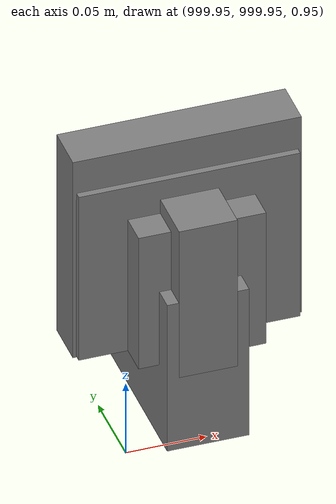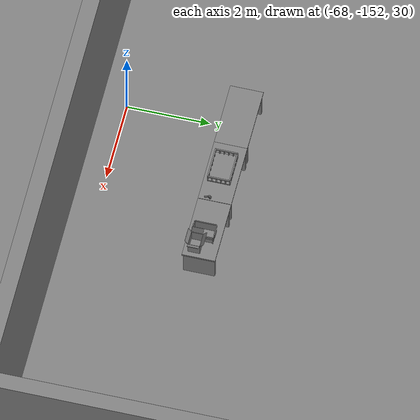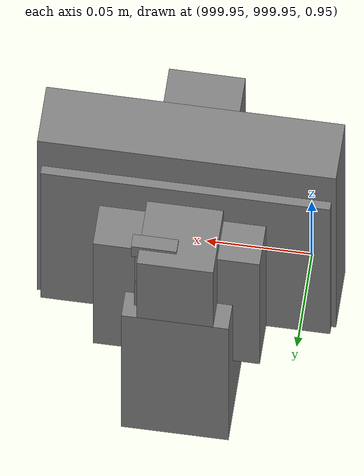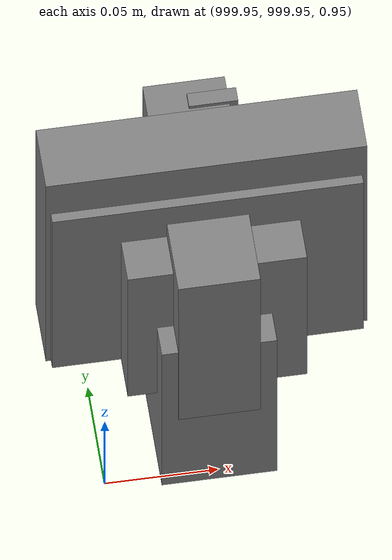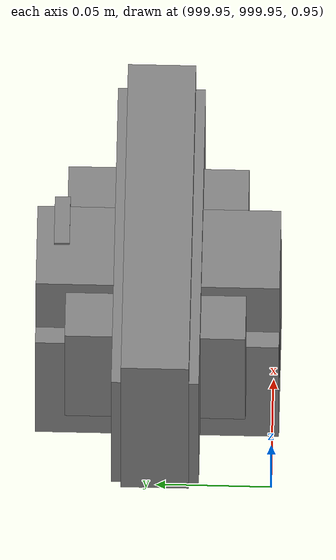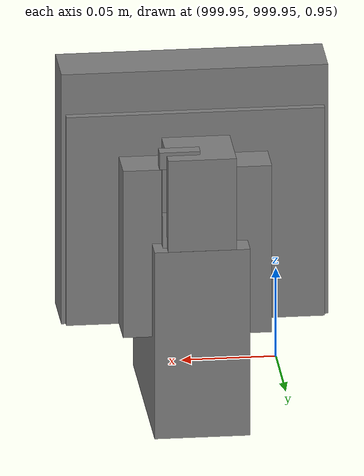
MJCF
<mujoco>
    <option gravity="0.000000000 0.000000000 -9.810000420" timestep="0.0049999999" integrator="implicitfast" density="1.225" viscosity="1.8000001e-05" noslip_iterations="10" iterations="100" sdf_iterations="50">
        <flag multiccd="disable"/>
    </option>
    <size memory="1000M"/>
    <compiler coordinate="local"/>
    <worldbody>
        <light cutoff="30" pos="0 1 1" dir="0 -1 -2"/>
        <light cutoff="30" pos="0 -1 1" dir="0 1 -2"/>
        <body pos="-64.866622925 -149.383972168 30.183746338" euler="89.999984741 89.999946594 0.000000000" name="openloong_gripper_2f85_fix_base_usda_bluebox_01">
            <geom contype="1" conaffinity="1" density="1000" type="box" material="" rgba="0.500000000 0.500000000 0.500000000 1.000000000" solimp="0.899999976 0.949999988 0.001000000" friction="1.000000000 0.005000000 0.000100000" solref="0.020000000 1.000000000" margin="0" condim="3" group="0" pos="0.276580811 0.187225342 0.000068665" quat="0.707106948 0.000077471 0.707106352 0.000077486" size="0.100000001 0.057999998 0.010000000" name="openloong_gripper_2f85_fix_base_usda_geom_69A8ED2D_0743_4A40_8608_1318312CBD31"/>
            <geom contype="1" conaffinity="1" density="1000" type="box" material="" rgba="0.500000000 0.500000000 0.500000000 1.000000000" solimp="0.899999976 0.949999988 0.001000000" friction="1.000000000 0.005000000 0.000100000" solref="0.020000000 1.000000000" margin="0" condim="3" group="0" pos="0.000000000 0.002883911 0.000000000" quat="0.999999881 0.000000000 0.000000000 0.000000000" size="0.254000008 0.003000000 0.172000006" name="openloong_gripper_2f85_fix_base_usda_geom_50F108AA_06FE_40DD_AD74_EE792D859ACF"/>
            <geom contype="1" conaffinity="1" density="1000" type="box" material="" rgba="0.500000000 0.500000000 0.500000000 1.000000000" solimp="0.899999976 0.949999988 0.001000000" friction="1.000000000 0.005000000 0.000100000" solref="0.020000000 1.000000000" margin="0" condim="3" group="0" pos="0.000000000 0.124874115 0.173484802" quat="0.999796331 0.020176515 -0.000000015 0.000000030" size="0.259999990 0.119999997 0.007000000" name="openloong_gripper_2f85_fix_base_usda_geom_B221E34F_1E6E_481B_875F_6CD2536912B7"/>
            <geom contype="1" conaffinity="1" density="1000" type="box" material="" rgba="0.500000000 0.500000000 0.500000000 1.000000000" solimp="0.899999976 0.949999988 0.001000000" friction="1.000000000 0.005000000 0.000100000" solref="0.020000000 1.000000000" margin="0" condim="3" group="0" pos="0.000000000 0.124874115 -0.173469543" quat="0.999796331 -0.020176545 -0.000000015 0.000000000" size="0.259999990 0.119999997 0.007000000" name="openloong_gripper_2f85_fix_base_usda_geom_8C094A10_6A57_4A02_A245_E0488DA87510"/>
            <geom contype="1" conaffinity="1" density="1000" type="box" material="" rgba="0.500000000 0.500000000 0.500000000 1.000000000" solimp="0.899999976 0.949999988 0.001000000" friction="1.000000000 0.005000000 0.000100000" solref="0.020000000 1.000000000" margin="0" condim="3" group="0" pos="0.000000000 0.214008331 0.188980103" quat="0.999912977 0.013176724 0.000000015 0.000000000" size="0.259999990 0.029999999 0.012500000" name="openloong_gripper_2f85_fix_base_usda_geom_FC9C3A69_3D55_4CC6_B957_9D8EDC860D37"/>
            <geom contype="1" conaffinity="1" density="1000" type="box" material="" rgba="0.500000000 0.500000000 0.500000000 1.000000000" solimp="0.899999976 0.949999988 0.001000000" friction="1.000000000 0.005000000 0.000100000" solref="0.020000000 1.000000000" margin="0" condim="3" group="0" pos="-0.258361816 0.125289917 0.001876831" quat="0.702796936 -0.020792112 0.710783124 0.020769298" size="0.189999998 0.119999997 0.009000000" name="openloong_gripper_2f85_fix_base_usda_geom_67D16A44_9EA9_4D53_B7B4_17F8C79AB082"/>
            <geom contype="1" conaffinity="1" density="1000" type="box" material="" rgba="0.500000000 0.500000000 0.500000000 1.000000000" solimp="0.899999976 0.949999988 0.001000000" friction="1.000000000 0.005000000 0.000100000" solref="0.020000000 1.000000000" margin="0" condim="3" group="0" pos="0.000000000 0.214008331 -0.188980103" quat="0.999912977 -0.013176769 0.000000030 0.000000015" size="0.259999990 0.029999999 0.012500000" name="openloong_gripper_2f85_fix_base_usda_geom_54596839_09D5_451F_A84A_4426B99E7584"/>
            <geom contype="1" conaffinity="1" density="1000" type="box" material="" rgba="0.500000000 0.500000000 0.500000000 1.000000000" solimp="0.899999976 0.949999988 0.001000000" friction="1.000000000 0.005000000 0.000100000" solref="0.020000000 1.000000000" margin="0" condim="3" group="0" pos="-0.276611328 0.187225342 0.000068665" quat="0.707106650 0.000077441 0.707106709 0.000077456" size="0.100000001 0.057999998 0.010000000" name="openloong_gripper_2f85_fix_base_usda_geom_83D6A0BB_BF68_4EC4_9BF1_A4ABF4B70C9E"/>
            <geom contype="1" conaffinity="1" density="1000" type="box" material="" rgba="0.500000000 0.500000000 0.500000000 1.000000000" solimp="0.899999976 0.949999988 0.001000000" friction="1.000000000 0.005000000 0.000100000" solref="0.020000000 1.000000000" margin="0" condim="3" group="0" pos="0.258331299 0.125289917 0.001876831" quat="0.702851415 0.018856421 0.710823774 -0.019329369" size="0.189999998 0.119999997 0.009000000" name="openloong_gripper_2f85_fix_base_usda_geom_2E8564BD_43EA_4065_89F9_B99511C29341"/>
            <freejoint name="openloong_gripper_2f85_fix_base_usda_bluebox_01_joint"/>
            <site size="0.005000000 0.005000000 0.005000000" rgba="0.500000000 0.500000000 0.500000000 1.000000000" pos="0.000000000 0.000000000 0.000000000" quat="0.999961913 0.008726534 0.000000000 0.000000000" group="0" type="sphere" name="openloong_gripper_2f85_fix_base_usda_bluebox_01site"/>
        </body>
        <body pos="-64.496299744 -149.491867065 30.235729218" euler="0.000000000 0.000000000 89.999946594" name="openloong_gripper_2f85_fix_base_usda_cardboardbox_01">
            <geom contype="1" conaffinity="1" density="1000" type="box" material="" rgba="0.500000000 0.500000000 0.500000000 1.000000000" solimp="0.899999976 0.949999988 0.001000000" friction="1.000000000 0.005000000 0.000100000" solref="0.020000000 1.000000000" margin="0" condim="3" group="0" pos="-0.003166199 -0.004086494 0.005052090" quat="1.000000000 0.000000000 0.000000000 0.000000000" size="0.142499998 0.177500010 0.005000000" name="openloong_gripper_2f85_fix_base_usda_geom_EA6C5712_2DB0_4F6A_936A_2FBB90B6EC96"/>
            <geom contype="1" conaffinity="1" density="1000" type="box" material="" rgba="0.500000000 0.500000000 0.500000000 1.000000000" solimp="0.899999976 0.949999988 0.001000000" friction="1.000000000 0.005000000 0.000100000" solref="0.020000000 1.000000000" margin="0" condim="3" group="0" pos="-0.003166199 0.170316696 0.150570869" quat="1.000000000 0.000000000 0.000000000 0.000000000" size="0.142499998 0.005000000 0.149999991" name="openloong_gripper_2f85_fix_base_usda_geom_A81CD3BB_4451_4B7C_A099_966A7F6E19AB"/>
            <geom contype="1" conaffinity="1" density="1000" type="box" material="" rgba="0.500000000 0.500000000 0.500000000 1.000000000" solimp="0.899999976 0.949999988 0.001000000" friction="1.000000000 0.005000000 0.000100000" solref="0.020000000 1.000000000" margin="0" condim="3" group="0" pos="-0.147399902 -0.005307198 0.150570869" quat="1.000000000 0.000000000 0.000000000 0.000000000" size="0.005000000 0.177500010 0.149999991" name="openloong_gripper_2f85_fix_base_usda_geom_D8CD3CA6_C000_4A8A_8176_37E1B9C23E6A"/>
            <geom contype="1" conaffinity="1" density="1000" type="box" material="" rgba="0.500000000 0.500000000 0.500000000 1.000000000" solimp="0.899999976 0.949999988 0.001000000" friction="1.000000000 0.005000000 0.000100000" solref="0.020000000 1.000000000" margin="0" condim="3" group="0" pos="0.140275955 -0.005307198 0.150570869" quat="1.000000000 0.000000000 0.000000000 0.000000000" size="0.005000000 0.177500010 0.149999991" name="openloong_gripper_2f85_fix_base_usda_geom_11991DB0_0059_4C6B_ADD5_14D6614F1E08"/>
            <geom contype="1" conaffinity="1" density="1000" type="box" material="" rgba="0.500000000 0.500000000 0.500000000 1.000000000" solimp="0.899999976 0.949999988 0.001000000" friction="1.000000000 0.005000000 0.000100000" solref="0.020000000 1.000000000" margin="0" condim="3" group="0" pos="-0.003166199 -0.181550980 0.150570869" quat="1.000000000 0.000000000 0.000000000 0.000000000" size="0.142499998 0.005000000 0.149999991" name="openloong_gripper_2f85_fix_base_usda_geom_F042350C_F197_46CF_8B6B_11C0541BF7F4"/>
            <freejoint name="openloong_gripper_2f85_fix_base_usda_cardboardbox_01_joint"/>
            <site size="0.005000000 0.005000000 0.005000000" rgba="0.500000000 0.500000000 0.500000000 1.000000000" pos="0.000000000 0.000000000 0.000000000" quat="0.999961913 0.008726535 0.000000000 0.000000000" group="0" type="sphere" name="openloong_gripper_2f85_fix_base_usda_site_B1639CAC_1BBA_48F0_8967_6DC497EE3BD5"/>
            <body pos="0.139160156 -0.004048347 0.301930904" euler="-179.999954224 49.383502960 179.999954224" name="openloong_gripper_2f85_fix_base_usda_A1_006">
                <geom contype="1" conaffinity="1" density="1000" type="box" material="" rgba="0.500000000 0.500000000 0.500000000 1.000000000" solimp="0.899999976 0.949999988 0.001000000" friction="1.000000000 0.005000000 0.000100000" solref="0.020000000 1.000000000" margin="0" condim="3" group="0" pos="-0.071587563 0.000009537 0.001745224" quat="0.999999881 0.000000000 0.000000000 0.000000000" size="0.071249999 0.179999992 0.002500000" name="openloong_gripper_2f85_fix_base_usda_geom_CEA20FD8_4DBD_4469_B853_53DA2FB1DED1"/>
                <joint armature="0" stiffness="0.07" damping="0.0099999998" axis="0.000000 1.000000 0.000000" type="hinge" name="openloong_gripper_2f85_fix_base_usda_A1_006"/>
            </body>
            <body pos="-0.145902634 -0.004086494 0.301938057" euler="-180.000000000 -60.000011444 -180.000000000" name="openloong_gripper_2f85_fix_base_usda_A2_006">
                <geom contype="1" conaffinity="1" density="1000" type="box" material="" rgba="0.500000000 0.500000000 0.500000000 1.000000000" solimp="0.899999976 0.949999988 0.001000000" friction="1.000000000 0.005000000 0.000100000" solref="0.020000000 1.000000000" margin="0" condim="3" group="0" pos="0.071268082 0.000009537 0.002717972" quat="0.000002921 0.000000000 -0.000000030 0.999999881" size="0.071249999 0.179999992 0.002500000" name="openloong_gripper_2f85_fix_base_usda_geom_E02E343F_FB2D_43FF_B477_F6CA861380F4"/>
                <joint armature="0" stiffness="0.07" damping="0.0099999998" axis="0.000000 1.000000 0.000000" type="hinge" name="openloong_gripper_2f85_fix_base_usda_A2_006"/>
            </body>
            <body pos="-0.003385544 0.175991058 0.301930904" euler="-125.858116150 -0.000004561 0.000002331" name="openloong_gripper_2f85_fix_base_usda_B2_006">
                <geom contype="1" conaffinity="1" density="1000" type="box" material="" rgba="0.500000000 0.500000000 0.500000000 1.000000000" solimp="0.899999976 0.949999988 0.001000000" friction="1.000000000 0.005000000 0.000100000" solref="0.020000000 1.000000000" margin="0" condim="3" group="0" pos="0.000009537 -0.070939064 -0.002470016" quat="0.999614120 0.027776197 -0.000000015 0.000000030" size="0.137500003 0.064999998 0.005000000" name="openloong_gripper_2f85_fix_base_usda_geom_D62BE52A_EE8F_4523_BD12_3C2929269727"/>
                <joint armature="0" stiffness="0.07" damping="0.0099999998" axis="1.000000 0.000000 0.000000" type="hinge" name="openloong_gripper_2f85_fix_base_usda_B2_006"/>
            </body>
            <body pos="-0.003385544 -0.184140205 0.301938057" euler="147.805557251 0.000000000 0.000000000" name="openloong_gripper_2f85_fix_base_usda_B1_006">
                <geom contype="1" conaffinity="1" density="1000" type="box" material="" rgba="0.500000000 0.500000000 0.500000000 1.000000000" solimp="0.899999976 0.949999988 0.001000000" friction="1.000000000 0.005000000 0.000100000" solref="0.020000000 1.000000000" margin="0" condim="3" group="0" pos="-0.000028610 0.070202351 -0.002703667" quat="0.999614179 -0.027776167 0.000000000 0.000000000" size="0.137500003 0.064999998 0.005000000" name="openloong_gripper_2f85_fix_base_usda_geom_DC20487B_56F3_4ED5_AAEF_040FBBB8A32C"/>
                <joint armature="0" stiffness="0.07" damping="0.0099999998" axis="1.000000 0.000000 0.000000" type="hinge" name="openloong_gripper_2f85_fix_base_usda_B1_006"/>
            </body>
        </body>
        <body pos="-65.882858276 -149.481979370 30.229999542" euler="-64.487716675 0.000000000 0.000000000" name="openloong_gripper_2f85_fix_base_usda_Barcode">
            <geom contype="1" conaffinity="1" density="1000" type="box" material="" rgba="0.500000000 0.500000000 0.500000000 1.000000000" solimp="0.899999976 0.949999988 0.001000000" friction="1.000000000 0.005000000 0.000100000" solref="0.020000000 1.000000000" margin="0" condim="3" group="0" pos="0.000000000 0.013038635 0.001419067" quat="0.000000000 0.000000000 0.000000000 1.000000119" size="0.034000002 0.010000000 0.017999999" name="openloong_gripper_2f85_fix_base_usda_geom_BE9A3F34_8425_4256_92F5_D51D677827E8"/>
            <geom contype="1" conaffinity="1" density="1000" type="box" material="" rgba="0.500000000 0.500000000 0.500000000 1.000000000" solimp="0.899999976 0.949999988 0.001000000" friction="1.000000000 0.005000000 0.000100000" solref="0.020000000 1.000000000" margin="0" condim="3" group="0" pos="0.000000000 -0.035301208 -0.007095337" quat="0.000000000 0.000000000 -0.043619365 0.999048233" size="0.028999999 0.010000000 0.020000000" name="openloong_gripper_2f85_fix_base_usda_geom_5AE87DCB_1E7F_433B_BD84_374001FD6028"/>
            <geom contype="1" conaffinity="1" density="1000" type="box" material="" rgba="0.500000000 0.500000000 0.500000000 1.000000000" solimp="0.899999976 0.949999988 0.001000000" friction="1.000000000 0.005000000 0.000100000" solref="0.020000000 1.000000000" margin="0" condim="3" group="0" pos="0.000000000 -0.043411255 -0.011749268" quat="0.922262907 0.386563420 0.000000000 0.000000000" size="0.026000001 0.010000000 0.020000000" name="openloong_gripper_2f85_fix_base_usda_geom_793FBD2B_8D88_4CA9_860B_268B5DD17FB7"/>
            <geom contype="1" conaffinity="1" density="1000" type="box" material="" rgba="0.500000000 0.500000000 0.500000000 1.000000000" solimp="0.899999976 0.949999988 0.001000000" friction="1.000000000 0.005000000 0.000100000" solref="0.020000000 1.000000000" margin="0" condim="3" group="0" pos="0.000000000 -0.016967773 -0.031860352" quat="0.000000000 0.000000000 0.000000000 1.000000119" size="0.008000000 0.010000000 0.013000000" name="openloong_gripper_2f85_fix_base_usda_geom_02E11F2A_5C4E_463B_A7EB_1B2805EC4088"/>
            <geom contype="1" conaffinity="1" density="1000" type="box" material="" rgba="0.500000000 0.500000000 0.500000000 1.000000000" solimp="0.899999976 0.949999988 0.001000000" friction="1.000000000 0.005000000 0.000100000" solref="0.020000000 1.000000000" margin="0" condim="3" group="0" pos="0.000000000 -0.001869202 0.000312805" quat="0.953716993 0.300705761 0.000000000 0.000000000" size="0.032000002 0.010000000 0.018999999" name="openloong_gripper_2f85_fix_base_usda_geom_E75DE77F_1972_4063_9ABB_9EB8C6374727"/>
            <geom contype="1" conaffinity="1" density="1000" type="box" material="" rgba="0.500000000 0.500000000 0.500000000 1.000000000" solimp="0.899999976 0.949999988 0.001000000" friction="1.000000000 0.005000000 0.000100000" solref="0.020000000 1.000000000" margin="0" condim="3" group="0" pos="0.000000000 -0.019531250 -0.003173828" quat="0.953716993 0.300705761 0.000000000 0.000000000" size="0.030999999 0.010000000 0.020000000" name="openloong_gripper_2f85_fix_base_usda_geom_4E26A372_DF21_418C_B749_0C42391CD75B"/>
            <geom contype="1" conaffinity="1" density="1000" type="box" material="" rgba="0.500000000 0.500000000 0.500000000 1.000000000" solimp="0.899999976 0.949999988 0.001000000" friction="1.000000000 0.005000000 0.000100000" solref="0.020000000 1.000000000" margin="0" condim="3" group="0" pos="0.000000000 -0.035301208 -0.007095337" quat="0.953716993 0.300705761 0.000000000 0.000000000" size="0.028999999 0.010000000 0.020000000" name="openloong_gripper_2f85_fix_base_usda_geom_3260F4EF_FAB9_4366_941C_FD70871A9BA0"/>
            <geom contype="1" conaffinity="1" density="1000" type="box" material="" rgba="0.500000000 0.500000000 0.500000000 1.000000000" solimp="0.899999976 0.949999988 0.001000000" friction="1.000000000 0.005000000 0.000100000" solref="0.020000000 1.000000000" margin="0" condim="3" group="0" pos="0.000000000 -0.042617798 -0.071121216" quat="0.000000000 0.000000000 0.000000000 1.000000119" size="0.013000000 0.021000000 0.059999999" name="openloong_gripper_2f85_fix_base_usda_geom_D1E5EEA3_E0AB_4EF5_AD69_A578E566DDEF"/>
            <freejoint name="openloong_gripper_2f85_fix_base_usda_Barcode_joint"/>
            <site size="0.005000000 0.005000000 0.005000000" rgba="0.500000000 0.500000000 0.500000000 1.000000000" pos="0.000000000 0.000000000 0.000000000" quat="1.000000000 0.000000000 0.000000000 0.000000000" group="0" type="sphere" name="openloong_gripper_2f85_fix_base_usda_Barcode_site"/>
        </body>
        <body pos="-66.745018005 -149.392349243 30.184000015" euler="0.000000000 0.000000000 89.999946594" name="[22333661630913]_Basket_01">
            <geom contype="1" conaffinity="1" density="1000" type="box" material="" rgba="0.500000000 0.500000000 0.500000000 1.000000000" solimp="0.899999976 0.949999988 0.001000000" friction="1.000000000 0.005000000 0.000100000" solref="0.020000000 1.000000000" margin="0" condim="3" group="0" pos="-0.052425385 0.389207840 0.089787483" quat="0.707107008 0.000000000 0.000000000 0.707106411" size="0.014249999 0.014249999 0.059999999" name="[22333661630913]_geom_BD129751_4506_4442_A428_32B6290A9A3D"/>
            <geom contype="1" conaffinity="1" density="1000" type="box" material="" rgba="0.500000000 0.500000000 0.500000000 1.000000000" solimp="0.899999976 0.949999988 0.001000000" friction="1.000000000 0.005000000 0.000100000" solref="0.020000000 1.000000000" margin="0" condim="3" group="0" pos="0.264015198 -0.133043289 0.089787483" quat="0.707107008 0.000000000 0.000000000 0.707106411" size="0.014249999 0.014249999 0.059999999" name="[22333661630913]_geom_FD052F47_CA06_46CA_AD15_7B3B91F52C26"/>
            <geom contype="1" conaffinity="1" density="1000" type="box" material="" rgba="0.500000000 0.500000000 0.500000000 1.000000000" solimp="0.899999976 0.949999988 0.001000000" friction="1.000000000 0.005000000 0.000100000" solref="0.020000000 1.000000000" margin="0" condim="3" group="0" pos="-0.264015198 -0.265548706 0.089793205" quat="0.707107008 0.000000000 0.000000000 0.707106411" size="0.014249999 0.014249999 0.059999999" name="[22333661630913]_geom_79924491_C4A6_4388_915E_75FDAE3BE820"/>
            <geom contype="1" conaffinity="1" density="1000" type="box" material="" rgba="0.500000000 0.500000000 0.500000000 1.000000000" solimp="0.899999976 0.949999988 0.001000000" friction="1.000000000 0.005000000 0.000100000" solref="0.020000000 1.000000000" margin="0" condim="3" group="0" pos="-0.160263062 -0.389322281 0.089793205" quat="0.707107008 0.000000000 0.000000000 0.707106411" size="0.014249999 0.014249999 0.059999999" name="[22333661630913]_geom_0E2E1B4E_A7BF_421C_BC31_CE0DE83773C1"/>
            <geom contype="1" conaffinity="1" density="1000" type="box" material="" rgba="0.500000000 0.500000000 0.500000000 1.000000000" solimp="0.899999976 0.949999988 0.001000000" friction="1.000000000 0.005000000 0.000100000" solref="0.020000000 1.000000000" margin="0" condim="3" group="0" pos="0.162265778 -0.389322281 0.089787483" quat="0.707107008 0.000000000 0.000000000 0.707106411" size="0.014249999 0.014249999 0.059999999" name="[22333661630913]_geom_97AD7B7A_70E1_46BE_AFD8_887EDBABE8FC"/>
            <geom contype="1" conaffinity="1" density="1000" type="box" material="" rgba="0.500000000 0.500000000 0.500000000 1.000000000" solimp="0.899999976 0.949999988 0.001000000" friction="1.000000000 0.005000000 0.000100000" solref="0.020000000 1.000000000" margin="0" condim="3" group="0" pos="0.264015198 0.389207840 0.089787483" quat="0.707107008 0.000000000 0.000000000 0.707106411" size="0.014249999 0.014249999 0.059999999" name="[22333661630913]_geom_0E9097B0_8DCA_450F_984A_E23DB0262FB6"/>
            <geom contype="1" conaffinity="1" density="1000" type="box" material="" rgba="0.500000000 0.500000000 0.500000000 1.000000000" solimp="0.899999976 0.949999988 0.001000000" friction="1.000000000 0.005000000 0.000100000" solref="0.020000000 1.000000000" margin="0" condim="3" group="0" pos="-0.264015198 -0.133043289 0.089793205" quat="0.707107008 0.000000000 0.000000000 0.707106411" size="0.014249999 0.014249999 0.059999999" name="[22333661630913]_geom_8D2108B4_C984_4AD7_979D_9569979B176F"/>
            <geom contype="1" conaffinity="1" density="1000" type="box" material="" rgba="0.500000000 0.500000000 0.500000000 1.000000000" solimp="0.899999976 0.949999988 0.001000000" friction="1.000000000 0.005000000 0.000100000" solref="0.020000000 1.000000000" margin="0" condim="3" group="0" pos="-0.264026642 0.269256592 0.089793205" quat="0.707107008 0.000000000 0.000000000 0.707106411" size="0.014249999 0.014249999 0.059999999" name="[22333661630913]_geom_B85D47FA_EEAF_454A_A150_AB23F8A459CA"/>
            <geom contype="1" conaffinity="1" density="1000" type="box" material="" rgba="0.500000000 0.500000000 0.500000000 1.000000000" solimp="0.899999976 0.949999988 0.001000000" friction="1.000000000 0.005000000 0.000100000" solref="0.020000000 1.000000000" margin="0" condim="3" group="0" pos="0.054462433 0.389207840 0.089787483" quat="0.707107008 0.000000000 0.000000000 0.707106411" size="0.014249999 0.014249999 0.059999999" name="[22333661630913]_geom_E328C00E_3819_4B58_9CA4_40ECEC47C2FD"/>
            <geom contype="1" conaffinity="1" density="1000" type="box" material="" rgba="0.500000000 0.500000000 0.500000000 1.000000000" solimp="0.899999976 0.949999988 0.001000000" friction="1.000000000 0.005000000 0.000100000" solref="0.020000000 1.000000000" margin="0" condim="3" group="0" pos="0.054462433 -0.389322281 0.089787483" quat="0.707107008 0.000000000 0.000000000 0.707106411" size="0.014249999 0.014249999 0.059999999" name="[22333661630913]_geom_4BD16463_8A5C_4713_ABF0_A22C48987D4E"/>
            <geom contype="1" conaffinity="1" density="1000" type="box" material="" rgba="0.500000000 0.500000000 0.500000000 1.000000000" solimp="0.899999976 0.949999988 0.001000000" friction="1.000000000 0.005000000 0.000100000" solref="0.020000000 1.000000000" margin="0" condim="3" group="0" pos="0.264015198 0.269256592 0.089793205" quat="0.707107008 0.000000000 0.000000000 0.707106411" size="0.014249999 0.014249999 0.059999999" name="[22333661630913]_geom_FD1A541C_FED7_4B93_84C9_CE8F5E461A9C"/>
            <geom contype="1" conaffinity="1" density="1000" type="box" material="" rgba="0.500000000 0.500000000 0.500000000 1.000000000" solimp="0.899999976 0.949999988 0.001000000" friction="1.000000000 0.005000000 0.000100000" solref="0.020000000 1.000000000" margin="0" condim="3" group="0" pos="0.264015198 -0.389322281 0.089787483" quat="0.707107008 0.000000000 0.000000000 0.707106411" size="0.014249999 0.014249999 0.059999999" name="[22333661630913]_geom_676B6F66_FD6C_4DFD_B5D1_6A62117C7790"/>
            <geom contype="1" conaffinity="1" density="1000" type="box" material="" rgba="0.500000000 0.500000000 0.500000000 1.000000000" solimp="0.899999976 0.949999988 0.001000000" friction="1.000000000 0.005000000 0.000100000" solref="0.020000000 1.000000000" margin="0" condim="3" group="0" pos="0.000000000 0.000000000 0.015998840" quat="0.707107008 0.000000000 0.000000000 0.707106411" size="0.403499991 0.279000014 0.015750000" name="[22333661630913]_geom_CA051540_A6C1_4A01_8C50_B39F17E1D1F5"/>
            <geom contype="1" conaffinity="1" density="1000" type="box" material="" rgba="0.500000000 0.500000000 0.500000000 1.000000000" solimp="0.899999976 0.949999988 0.001000000" friction="1.000000000 0.005000000 0.000100000" solref="0.020000000 1.000000000" margin="0" condim="3" group="0" pos="0.000000000 -0.389476776 0.163619041" quat="0.707107008 0.000000000 0.000000000 0.707106411" size="0.015000000 0.277500004 0.015750000" name="[22333661630913]_geom_BFDF6159_A53C_44C9_9EE4_AB05D9422334"/>
            <geom contype="1" conaffinity="1" density="1000" type="box" material="" rgba="0.500000000 0.500000000 0.500000000 1.000000000" solimp="0.899999976 0.949999988 0.001000000" friction="1.000000000 0.005000000 0.000100000" solref="0.020000000 1.000000000" margin="0" condim="3" group="0" pos="0.162265778 0.389207840 0.089787483" quat="0.707107008 0.000000000 0.000000000 0.707106411" size="0.014249999 0.014249999 0.059999999" name="[22333661630913]_geom_5E41C4A2_9840_4229_8966_3E5AF077CC3C"/>
            <geom contype="1" conaffinity="1" density="1000" type="box" material="" rgba="0.500000000 0.500000000 0.500000000 1.000000000" solimp="0.899999976 0.949999988 0.001000000" friction="1.000000000 0.005000000 0.000100000" solref="0.020000000 1.000000000" margin="0" condim="3" group="0" pos="0.000000000 0.389471054 0.163619041" quat="0.707107008 0.000000000 0.000000000 0.707106411" size="0.015000000 0.277500004 0.015750000" name="[22333661630913]_geom_79732462_732E_4B04_BD55_9AA9F5DF2BD2"/>
            <geom contype="1" conaffinity="1" density="1000" type="box" material="" rgba="0.500000000 0.500000000 0.500000000 1.000000000" solimp="0.899999976 0.949999988 0.001000000" friction="1.000000000 0.005000000 0.000100000" solref="0.020000000 1.000000000" margin="0" condim="3" group="0" pos="-0.263511658 0.000000000 0.163619041" quat="0.707107008 0.000000000 0.000000000 0.707106411" size="0.403499991 0.015000000 0.015750000" name="[22333661630913]_geom_CB505ECE_493C_4A7E_9F08_0BBA545435AF"/>
            <geom contype="1" conaffinity="1" density="1000" type="box" material="" rgba="0.500000000 0.500000000 0.500000000 1.000000000" solimp="0.899999976 0.949999988 0.001000000" friction="1.000000000 0.005000000 0.000100000" solref="0.020000000 1.000000000" margin="0" condim="3" group="0" pos="-0.264015198 0.141334534 0.089793205" quat="0.707107008 0.000000000 0.000000000 0.707106411" size="0.014249999 0.014249999 0.059999999" name="[22333661630913]_geom_086B0E4C_0394_425D_A87B_ACBD41B30706"/>
            <geom contype="1" conaffinity="1" density="1000" type="box" material="" rgba="0.500000000 0.500000000 0.500000000 1.000000000" solimp="0.899999976 0.949999988 0.001000000" friction="1.000000000 0.005000000 0.000100000" solref="0.020000000 1.000000000" margin="0" condim="3" group="0" pos="0.264015198 -0.265548706 0.089787483" quat="0.707107008 0.000000000 0.000000000 0.707106411" size="0.014249999 0.014249999 0.059999999" name="[22333661630913]_geom_2B850FAA_9410_40AE_93AE_DC48F5A68630"/>
            <geom contype="1" conaffinity="1" density="1000" type="box" material="" rgba="0.500000000 0.500000000 0.500000000 1.000000000" solimp="0.899999976 0.949999988 0.001000000" friction="1.000000000 0.005000000 0.000100000" solref="0.020000000 1.000000000" margin="0" condim="3" group="0" pos="-0.160263062 0.389207840 0.089787483" quat="0.707107008 0.000000000 0.000000000 0.707106411" size="0.014249999 0.014249999 0.059999999" name="[22333661630913]_geom_B665BE21_A95D_481C_8B01_3464EA649FB7"/>
            <geom contype="1" conaffinity="1" density="1000" type="box" material="" rgba="0.500000000 0.500000000 0.500000000 1.000000000" solimp="0.899999976 0.949999988 0.001000000" friction="1.000000000 0.005000000 0.000100000" solref="0.020000000 1.000000000" margin="0" condim="3" group="0" pos="-0.052425385 -0.389322281 0.089787483" quat="0.707107008 0.000000000 0.000000000 0.707106411" size="0.014249999 0.014249999 0.059999999" name="[22333661630913]_geom_950A9440_FDFB_45B6_9761_7211D51BF34C"/>
            <geom contype="1" conaffinity="1" density="1000" type="box" material="" rgba="0.500000000 0.500000000 0.500000000 1.000000000" solimp="0.899999976 0.949999988 0.001000000" friction="1.000000000 0.005000000 0.000100000" solref="0.020000000 1.000000000" margin="0" condim="3" group="0" pos="-0.264026642 -0.389322281 0.089793205" quat="0.707107008 0.000000000 0.000000000 0.707106411" size="0.014249999 0.014249999 0.059999999" name="[22333661630913]_geom_3AB5E4C2_9F3A_4D52_B4E9_1641B890E9CD"/>
            <geom contype="1" conaffinity="1" density="1000" type="box" material="" rgba="0.500000000 0.500000000 0.500000000 1.000000000" solimp="0.899999976 0.949999988 0.001000000" friction="1.000000000 0.005000000 0.000100000" solref="0.020000000 1.000000000" margin="0" condim="3" group="0" pos="0.264015198 0.141334534 0.089787483" quat="0.707107008 0.000000000 0.000000000 0.707106411" size="0.014249999 0.014249999 0.059999999" name="[22333661630913]_geom_786A2F99_4542_4D2F_A24B_8FA9CE78F20D"/>
            <geom contype="1" conaffinity="1" density="1000" type="box" material="" rgba="0.500000000 0.500000000 0.500000000 1.000000000" solimp="0.899999976 0.949999988 0.001000000" friction="1.000000000 0.005000000 0.000100000" solref="0.020000000 1.000000000" margin="0" condim="3" group="0" pos="-0.264015198 0.389207840 0.089793205" quat="0.707107008 0.000000000 0.000000000 0.707106411" size="0.014249999 0.014249999 0.059999999" name="[22333661630913]_geom_B999BE99_E7EF_45F8_9D8A_394BF6DB82F4"/>
            <geom contype="1" conaffinity="1" density="1000" type="box" material="" rgba="0.500000000 0.500000000 0.500000000 1.000000000" solimp="0.899999976 0.949999988 0.001000000" friction="1.000000000 0.005000000 0.000100000" solref="0.020000000 1.000000000" margin="0" condim="3" group="0" pos="0.264015198 0.004480362 0.089787483" quat="0.707107008 0.000000000 0.000000000 0.707106411" size="0.014249999 0.014249999 0.059999999" name="[22333661630913]_geom_D58997B5_2360_4E55_BB73_7BDB790871BB"/>
            <geom contype="1" conaffinity="1" density="1000" type="box" material="" rgba="0.500000000 0.500000000 0.500000000 1.000000000" solimp="0.899999976 0.949999988 0.001000000" friction="1.000000000 0.005000000 0.000100000" solref="0.020000000 1.000000000" margin="0" condim="3" group="0" pos="0.263694763 -0.000011444 0.163619041" quat="0.707107008 0.000000000 0.000000000 0.707106411" size="0.403499991 0.015000000 0.015750000" name="[22333661630913]_geom_35714D6F_D5D4_4A42_B2E4_B018298C9909"/>
            <geom contype="1" conaffinity="1" density="1000" type="box" material="" rgba="0.500000000 0.500000000 0.500000000 1.000000000" solimp="0.899999976 0.949999988 0.001000000" friction="1.000000000 0.005000000 0.000100000" solref="0.020000000 1.000000000" margin="0" condim="3" group="0" pos="-0.264015198 0.004480362 0.089793205" quat="0.707107008 0.000000000 0.000000000 0.707106411" size="0.014249999 0.014249999 0.059999999" name="[22333661630913]_geom_A1A895A7_F329_40A8_B1E5_A322F1094CCB"/>
            <freejoint name="[22333661630913]_joint_5DD22E68_DC41_4269_AEE0_3E5CA1AD46FA"/>
        </body>
        <body pos="0.000000000 0.000000000 0.000000000" euler="0.000000000 0.000000000 0.000000000" name="Static Objects_Static Objects">
            <geom contype="1" conaffinity="1" density="1000" type="box" material="" rgba="0.500000000 0.500000000 0.500000000 1.000000000" solimp="0.899999976 0.949999988 0.001000000" friction="1.000000000 0.005000000 0.000100000" solref="0.020000000 1.000000000" margin="0" condim="3" group="0" pos="-67.544113159 -149.365814209 29.727830887" quat="0.500000417 0.499999970 0.499999553 0.499999970" size="0.381000012 0.319999993 0.041000001" name="Static Objects_geom_7E17372B_8605_48AA_A266_E1DFF999A77F"/>
            <geom contype="1" conaffinity="1" density="1000" type="box" material="" rgba="0.500000000 0.500000000 0.500000000 1.000000000" solimp="0.899999976 0.949999988 0.001000000" friction="1.000000000 0.005000000 0.000100000" solref="0.020000000 1.000000000" margin="0" condim="3" group="0" pos="-68.239501953 -149.365814209 30.086868286" quat="0.500000417 0.499999970 0.499999553 0.499999970" size="0.370999992 0.039500002 0.745000005" name="Static Objects_geom_82C3235D_59A0_47FA_AFC6_EA6850FD4064"/>
            <geom contype="1" conaffinity="1" density="1000" type="box" material="" rgba="0.500000000 0.500000000 0.500000000 1.000000000" solimp="0.899999976 0.949999988 0.001000000" friction="1.000000000 0.005000000 0.000100000" solref="0.020000000 1.000000000" margin="0" condim="3" group="0" pos="-68.239501953 -149.365814209 30.147235870" quat="0.500000417 0.499999970 0.499999553 0.499999970" size="0.400000006 0.022000000 0.800000012" name="Static Objects_geom_B3AB5052_2966_4ECD_AD92_86A98BBAF1C5"/>
            <geom contype="1" conaffinity="1" density="1000" type="box" material="" rgba="0.500000000 0.500000000 0.500000000 1.000000000" solimp="0.899999976 0.949999988 0.001000000" friction="1.000000000 0.005000000 0.000100000" solref="0.020000000 1.000000000" margin="0" condim="3" group="0" pos="-68.934890747 -149.365814209 29.727830887" quat="0.500000417 0.499999970 0.499999553 0.499999970" size="0.381000012 0.319999993 0.041000001" name="Static Objects_geom_C4C25B2B_4AC3_487F_B0BE_E670809A202C"/>
            <geom contype="1" conaffinity="1" density="1000" type="box" material="" rgba="0.500000000 0.500000000 0.500000000 1.000000000" solimp="0.899999976 0.949999988 0.001000000" friction="1.000000000 0.005000000 0.000100000" solref="0.020000000 1.000000000" margin="0" condim="3" group="0" pos="-68.239501953 -149.365814209 29.561563492" quat="0.500000417 0.499999970 0.499999553 0.499999970" size="0.020000000 0.022000000 0.660000026" name="Static Objects_geom_19C30F31_0121_40DD_BFB0_73D565FC3B42"/>
            <geom contype="1" conaffinity="1" density="1000" type="box" material="" rgba="0.500000000 0.500000000 0.500000000 1.000000000" solimp="0.899999976 0.949999988 0.001000000" friction="1.000000000 0.005000000 0.000100000" solref="0.020000000 1.000000000" margin="0" condim="3" group="0" pos="-65.945671082 -149.365814209 29.727830887" quat="0.500000417 0.499999970 0.499999553 0.499999970" size="0.381000012 0.319999993 0.041000001" name="Static Objects_geom_F421C7F3_16B5_4BD7_A5F4_BE33F4C67DEA"/>
            <geom contype="1" conaffinity="1" density="1000" type="box" material="" rgba="0.500000000 0.500000000 0.500000000 1.000000000" solimp="0.899999976 0.949999988 0.001000000" friction="1.000000000 0.005000000 0.000100000" solref="0.020000000 1.000000000" margin="0" condim="3" group="0" pos="-66.641059875 -149.365814209 30.086868286" quat="0.500000417 0.499999970 0.499999553 0.499999970" size="0.370999992 0.039500002 0.745000005" name="Static Objects_geom_E654567E_60BC_41FE_84BA_7C985D571CAD"/>
            <geom contype="1" conaffinity="1" density="1000" type="box" material="" rgba="0.500000000 0.500000000 0.500000000 1.000000000" solimp="0.899999976 0.949999988 0.001000000" friction="1.000000000 0.005000000 0.000100000" solref="0.020000000 1.000000000" margin="0" condim="3" group="0" pos="-66.641059875 -149.365814209 30.147235870" quat="0.500000417 0.499999970 0.499999553 0.499999970" size="0.400000006 0.022000000 0.800000012" name="Static Objects_geom_56F42B1B_3A26_4FF9_8086_F9D8E95BE851"/>
            <geom contype="1" conaffinity="1" density="1000" type="box" material="" rgba="0.500000000 0.500000000 0.500000000 1.000000000" solimp="0.899999976 0.949999988 0.001000000" friction="1.000000000 0.005000000 0.000100000" solref="0.020000000 1.000000000" margin="0" condim="3" group="0" pos="-67.336448669 -149.365814209 29.727830887" quat="0.500000417 0.499999970 0.499999553 0.499999970" size="0.381000012 0.319999993 0.041000001" name="Static Objects_geom_871A4E66_5B39_4461_A208_01706CF2ECB2"/>
            <geom contype="1" conaffinity="1" density="1000" type="box" material="" rgba="0.500000000 0.500000000 0.500000000 1.000000000" solimp="0.899999976 0.949999988 0.001000000" friction="1.000000000 0.005000000 0.000100000" solref="0.020000000 1.000000000" margin="0" condim="3" group="0" pos="-66.641059875 -149.365814209 29.561563492" quat="0.500000417 0.499999970 0.499999553 0.499999970" size="0.020000000 0.022000000 0.660000026" name="Static Objects_geom_2AFB2F25_4800_4325_A3DC_A8296C46B442"/>
            <geom contype="1" conaffinity="1" density="1000" type="box" material="" rgba="0.500000000 0.500000000 0.500000000 1.000000000" solimp="0.899999976 0.949999988 0.001000000" friction="1.000000000 0.005000000 0.000100000" solref="0.020000000 1.000000000" margin="0" condim="3" group="0" pos="-64.338577271 -149.365814209 29.727830887" quat="0.500000417 0.499999970 0.499999553 0.499999970" size="0.381000012 0.319999993 0.041000001" name="Static Objects_geom_67738A36_1F54_4924_9BE9_C074390A5223"/>
            <geom contype="1" conaffinity="1" density="1000" type="box" material="" rgba="0.500000000 0.500000000 0.500000000 1.000000000" solimp="0.899999976 0.949999988 0.001000000" friction="1.000000000 0.005000000 0.000100000" solref="0.020000000 1.000000000" margin="0" condim="3" group="0" pos="-65.033966064 -149.365814209 30.086868286" quat="0.500000417 0.499999970 0.499999553 0.499999970" size="0.370999992 0.039500002 0.745000005" name="Static Objects_geom_8AD71235_794E_4E30_8171_37B34CE0CDEC"/>
            <geom contype="1" conaffinity="1" density="1000" type="box" material="" rgba="0.500000000 0.500000000 0.500000000 1.000000000" solimp="0.899999976 0.949999988 0.001000000" friction="1.000000000 0.005000000 0.000100000" solref="0.020000000 1.000000000" margin="0" condim="3" group="0" pos="-65.033966064 -149.365814209 30.147235870" quat="0.500000417 0.499999970 0.499999553 0.499999970" size="0.400000006 0.022000000 0.800000012" name="Static Objects_geom_6440D606_2C53_46FA_8DC2_D97EB4F63066"/>
            <geom contype="1" conaffinity="1" density="1000" type="box" material="" rgba="0.500000000 0.500000000 0.500000000 1.000000000" solimp="0.899999976 0.949999988 0.001000000" friction="1.000000000 0.005000000 0.000100000" solref="0.020000000 1.000000000" margin="0" condim="3" group="0" pos="-65.729354858 -149.365814209 29.727830887" quat="0.500000417 0.499999970 0.499999553 0.499999970" size="0.381000012 0.319999993 0.041000001" name="Static Objects_geom_9091A400_E208_47A7_AEF5_1A59DF1BD4C5"/>
            <geom contype="1" conaffinity="1" density="1000" type="box" material="" rgba="0.500000000 0.500000000 0.500000000 1.000000000" solimp="0.899999976 0.949999988 0.001000000" friction="1.000000000 0.005000000 0.000100000" solref="0.020000000 1.000000000" margin="0" condim="3" group="0" pos="-65.033966064 -149.365814209 29.561563492" quat="0.500000417 0.499999970 0.499999553 0.499999970" size="0.020000000 0.022000000 0.660000026" name="Static Objects_geom_7491F5C9_ECBE_4D47_A1D2_E0F72A2A4F8B"/>
            <geom contype="1" conaffinity="1" density="1000" type="box" material="" rgba="0.500000000 0.500000000 0.500000000 1.000000000" solimp="0.899999976 0.949999988 0.001000000" friction="1.000000000 0.005000000 0.000100000" solref="0.020000000 1.000000000" margin="0" condim="3" group="0" pos="-61.754566193 -137.853729248 33.906845093" quat="0.707107067 0.000000000 0.000000000 0.707106471" size="0.759999990 0.759999990 4.500000000" name="Static Objects_geom_044CE6E2_1F4D_424B_A7D0_511182F25826"/>
            <geom contype="1" conaffinity="1" density="1000" type="box" material="" rgba="0.500000000 0.500000000 0.500000000 1.000000000" solimp="0.899999976 0.949999988 0.001000000" friction="1.000000000 0.005000000 0.000100000" solref="0.020000000 1.000000000" margin="0" condim="3" group="0" pos="-57.511135101 -144.927108765 31.707921982" quat="1.000000000 0.000000000 0.000000000 0.000000000" size="0.200000003 8.000000000 2.299999952" name="Static Objects_geom_78D6B5CC_11A8_430A_9E1D_2A885DB3EB9F"/>
            <geom contype="1" conaffinity="1" density="1000" type="box" material="" rgba="0.500000000 0.500000000 0.500000000 1.000000000" solimp="0.899999976 0.949999988 0.001000000" friction="1.000000000 0.005000000 0.000100000" solref="0.020000000 1.000000000" margin="0" condim="3" group="0" pos="-80.517646790 -157.574050903 31.688196182" quat="0.707107067 0.000000000 0.000000000 0.707106471" size="0.600000024 0.600000024 2.299999952" name="Static Objects_geom_CA4D6E17_4A8E_4BCA_8715_AB608F8F77C8"/>
            <geom contype="1" conaffinity="1" density="1000" type="box" material="" rgba="0.500000000 0.500000000 0.500000000 1.000000000" solimp="0.899999976 0.949999988 0.001000000" friction="1.000000000 0.005000000 0.000100000" solref="0.020000000 1.000000000" margin="0" condim="3" group="0" pos="-80.711044312 -147.414932251 31.666158676" quat="1.000000000 0.000000000 0.000000000 0.000000000" size="0.200000003 10.000000000 2.299999952" name="Static Objects_geom_7BF8C6F9_9C21_46CE_9321_D7E9C87BFF37"/>
            <geom contype="1" conaffinity="1" density="1000" type="box" material="" rgba="0.500000000 0.500000000 0.500000000 1.000000000" solimp="0.899999976 0.949999988 0.001000000" friction="1.000000000 0.005000000 0.000100000" solref="0.020000000 1.000000000" margin="0" condim="3" group="0" pos="-57.687217712 -137.434692383 31.688196182" quat="0.707107067 0.000000000 0.000000000 0.707106471" size="0.600000024 0.600000024 2.299999952" name="Static Objects_geom_792FCDC0_6988_49CA_BE88_8DBBFA715195"/>
            <geom contype="1" conaffinity="1" density="1000" type="box" material="" rgba="0.500000000 0.500000000 0.500000000 1.000000000" solimp="0.899999976 0.949999988 0.001000000" friction="1.000000000 0.005000000 0.000100000" solref="0.020000000 1.000000000" margin="0" condim="3" group="0" pos="-69.537033081 -140.263229370 31.714921951" quat="0.707107067 0.000000000 0.000000000 0.707106471" size="0.759999990 4.500000000 2.299999952" name="Static Objects_geom_8EB357AA_9910_4C3A_9818_D8383ED0486F"/>
            <geom contype="1" conaffinity="1" density="1000" type="box" material="" rgba="0.500000000 0.500000000 0.500000000 1.000000000" solimp="0.899999976 0.949999988 0.001000000" friction="1.000000000 0.005000000 0.000100000" solref="0.020000000 1.000000000" margin="0" condim="3" group="0" pos="-80.073638916 -137.853713989 33.906845093" quat="0.707107067 0.000000000 0.000000000 0.707106471" size="0.759999990 0.759999990 4.500000000" name="Static Objects_geom_EDAB118E_B12B_4C2B_A928_06751E9C0F31"/>
            <geom contype="1" conaffinity="1" density="1000" type="box" material="" rgba="0.500000000 0.500000000 0.500000000 1.000000000" solimp="0.899999976 0.949999988 0.001000000" friction="1.000000000 0.005000000 0.000100000" solref="0.020000000 1.000000000" margin="0" condim="3" group="0" pos="-73.406707764 -155.734664917 31.707921982" quat="1.000000000 0.000000000 0.000000000 0.000000000" size="0.200000003 3.000000000 2.299999952" name="Static Objects_geom_034B33F5_F7A0_4B68_A6EC_17A10A58F67A"/>
            <geom contype="1" conaffinity="1" density="1000" type="box" material="" rgba="0.500000000 0.500000000 0.500000000 1.000000000" solimp="0.899999976 0.949999988 0.001000000" friction="1.000000000 0.005000000 0.000100000" solref="0.020000000 1.000000000" margin="0" condim="3" group="0" pos="-68.497543335 -137.448257446 31.707921982" quat="0.707107067 0.000000000 0.000000000 0.707106471" size="0.200000003 14.000000000 2.299999952" name="Static Objects_geom_E0302AA9_2BBA_4C15_96D1_51900C829D77"/>
            <geom contype="1" conaffinity="1" density="1000" type="cylinder" material="" rgba="0.500000000 0.500000000 0.500000000 1.000000000" solimp="0.899999976 0.949999988 0.001000000" friction="1.000000000 0.005000000 0.000100000" solref="0.020000000 1.000000000" margin="0" condim="3" group="0" pos="-68.868522644 -142.134506226 31.711090088" quat="0.707107067 0.000000000 0.000000000 0.707106471" size="0.509999990 2.299999952 1.000000000" name="Static Objects_geom_7156101E_7238_4115_9DA8_384260A04192"/>
            <geom contype="1" conaffinity="1" density="1000" type="plane" material="" rgba="0.500000000 0.500000000 0.500000000 1.000000000" solimp="0.899999976 0.949999988 0.001000000" friction="1.000000000 0.005000000 0.000100000" solref="0.020000000 1.000000000" margin="0" condim="3" group="0" pos="-72.873703003 -147.131927490 29.409669876" quat="1.000000000 0.000000000 0.000000000 0.000000000" size="18.000000000 14.000000000 1.000000000" name="Static Objects_geom_ABADB12E_DEA3_4B1D_850B_550894403A62"/>
            <geom contype="1" conaffinity="1" density="1000" type="box" material="" rgba="0.500000000 0.500000000 0.500000000 1.000000000" solimp="0.899999976 0.949999988 0.001000000" friction="1.000000000 0.005000000 0.000100000" solref="0.020000000 1.000000000" margin="0" condim="3" group="0" pos="-79.943580627 -157.782272339 31.707921982" quat="0.707107067 0.000000000 0.000000000 0.707106471" size="0.200000003 7.000000000 2.299999952" name="Static Objects_geom_67EDADAD_EAF8_4B02_9B5D_D758B21C90FB"/>
            <geom contype="1" conaffinity="1" density="1000" type="box" material="" rgba="0.500000000 0.500000000 0.500000000 1.000000000" solimp="0.899999976 0.949999988 0.001000000" friction="1.000000000 0.005000000 0.000100000" solref="0.020000000 1.000000000" margin="0" condim="3" group="0" pos="-65.421028137 -152.903442383 31.707921982" quat="0.707107067 0.000000000 0.000000000 0.707106471" size="0.200000003 7.800000191 2.299999952" name="Static Objects_geom_48310D94_336D_4F3F_8A60_C8F8913684FC"/>
            <geom contype="1" conaffinity="1" density="1000" type="box" material="" rgba="0.500000000 0.500000000 0.500000000 1.000000000" solimp="0.899999976 0.949999988 0.001000000" friction="1.000000000 0.005000000 0.000100000" solref="0.020000000 1.000000000" margin="0" condim="3" group="0" pos="-74.776908875 -149.964416504 31.688196182" quat="1.000000000 0.000000000 0.000000000 0.000000000" size="0.600000024 0.409999996 2.299999952" name="Static Objects_geom_E416C241_0A5E_468A_8F37_B7B033EE4D7C"/>
            <geom contype="1" conaffinity="1" density="1000" type="cylinder" material="" rgba="0.500000000 0.500000000 0.500000000 1.000000000" solimp="0.899999976 0.949999988 0.001000000" friction="1.000000000 0.005000000 0.000100000" solref="0.020000000 1.000000000" margin="0" condim="3" group="0" pos="-60.161884308 -142.134506226 31.711090088" quat="0.707107067 0.000000000 0.000000000 0.707106471" size="0.509999990 2.299999952 1.000000000" name="Static Objects_geom_DD1D4344_BF85_4669_BAE7_9CB8F46F66E3"/>
            <geom contype="1" conaffinity="1" density="1000" type="cylinder" material="" rgba="0.500000000 0.500000000 0.500000000 1.000000000" solimp="0.899999976 0.949999988 0.001000000" friction="1.000000000 0.005000000 0.000100000" solref="0.020000000 1.000000000" margin="0" condim="3" group="0" pos="-75.382453918 -149.963455200 31.711090088" quat="0.707107067 0.000000000 0.000000000 0.707106471" size="0.409999996 2.299999952 1.000000000" name="Static Objects_geom_80219D21_BEC1_46D7_87FA_48C054FDE80C"/>
            <geom contype="1" conaffinity="1" density="1000" type="cylinder" material="" rgba="0.500000000 0.500000000 0.500000000 1.000000000" solimp="0.899999976 0.949999988 0.001000000" friction="1.000000000 0.005000000 0.000100000" solref="0.020000000 1.000000000" margin="0" condim="3" group="0" pos="-74.154960632 -149.963455200 31.711090088" quat="0.707107067 0.000000000 0.000000000 0.707106471" size="0.409999996 2.299999952 1.000000000" name="Static Objects_geom_5665E4D0_E98C_4F83_A797_8A124C360075"/>
            <geom contype="1" conaffinity="1" density="1000" type="cylinder" material="" rgba="0.500000000 0.500000000 0.500000000 1.000000000" solimp="0.899999976 0.949999988 0.001000000" friction="1.000000000 0.005000000 0.000100000" solref="0.020000000 1.000000000" margin="0" condim="3" group="0" pos="-77.566612244 -142.134506226 31.711090088" quat="0.707107067 0.000000000 0.000000000 0.707106471" size="0.509999990 2.299999952 1.000000000" name="Static Objects_geom_BF1AD90A_0A4C_4E2F_BA53_D4D54CD8B10F"/>
        </body>
        <body pos="1000.000000000 999.999938965 1.000000000" euler="0.000000000 0.000000000 180.000000000" name="openloong_gripper_2f85_fix_base_usda_intelcore_i5">
            <geom contype="1" conaffinity="1" density="1000" type="box" material="" rgba="0.500000000 0.500000000 0.500000000 1.000000000" solimp="0.899999976 0.949999988 0.001000000" friction="1.000000000 0.005000000 0.000100000" solref="0.020000000 1.000000000" margin="0" condim="3" group="0" pos="0.000000000 0.000000000 0.051722717" quat="0.707106709 0.000000000 0.000000000 -0.707106769" size="0.052800000 0.018080002 0.052800000" name="openloong_gripper_2f85_fix_base_usda_geom_B469F61E_7037_4E7F_AECD_DB957A48FD1B"/>
            <freejoint name="openloong_gripper_2f85_fix_base_usda_intelcore_i5_joint"/>
            <site size="0.005000000 0.005000000 0.005000000" rgba="0.500000000 0.500000000 0.500000000 1.000000000" pos="0.000000000 0.000000000 0.000000000" quat="0.999961913 0.008726534 0.000000000 0.000000000" group="0" type="sphere" name="openloong_gripper_2f85_fix_base_usda_intelcore_i5site"/>
        </body>
        <body pos="-65.980468750 -149.092376709 31.168027878" euler="128.897857666 2.877812862 -4.805933475" mocap="true" name="spotlight4_SpotLight"/>
        <body pos="1000.000000000 1000.000000000 1.000000000" euler="0.000000000 0.000000000 180.000000000" name="openloong_gripper_2f85_fix_base_usda_battery_01">
            <geom contype="1" conaffinity="1" density="1000" type="box" material="" rgba="0.500000000 0.500000000 0.500000000 1.000000000" solimp="0.899999976 0.949999988 0.001000000" friction="1.000000000 0.005000000 0.000100000" solref="0.020000000 1.000000000" margin="0" condim="3" group="0" pos="-0.011123657 -0.041940309 0.101691343" quat="1.000000000 0.000000000 0.000000000 0.000000000" size="0.010800000 0.003375000 0.004725000" name="openloong_gripper_2f85_fix_base_usda_geom_DE973191_927D_4C65_B8EF_34756817C1B0"/>
            <geom contype="1" conaffinity="1" density="1000" type="box" material="" rgba="0.500000000 0.500000000 0.500000000 1.000000000" solimp="0.899999976 0.949999988 0.001000000" friction="1.000000000 0.005000000 0.000100000" solref="0.020000000 1.000000000" margin="0" condim="3" group="0" pos="-0.010876465 -0.044247437 0.047066893" quat="0.998702705 -0.050920475 0.000000000 0.000000000" size="0.009450001 0.002700000 0.024975000" name="openloong_gripper_2f85_fix_base_usda_geom_4D25429A_8426_442D_99B5_393EBCE65078"/>
            <geom contype="1" conaffinity="1" density="1000" type="box" material="" rgba="0.500000000 0.500000000 0.500000000 1.000000000" solimp="0.899999976 0.949999988 0.001000000" friction="1.000000000 0.005000000 0.000100000" solref="0.020000000 1.000000000" margin="0" condim="3" group="0" pos="-0.001235962 -0.000659180 0.047381196" quat="1.000000000 0.000000000 0.000000000 0.000000000" size="0.039420001 0.039150000 0.047250003" name="openloong_gripper_2f85_fix_base_usda_geom_207FC39E_7BE7_4974_9457_35886ABD447F"/>
            <geom contype="1" conaffinity="1" density="1000" type="box" material="" rgba="0.500000000 0.500000000 0.500000000 1.000000000" solimp="0.899999976 0.949999988 0.001000000" friction="1.000000000 0.005000000 0.000100000" solref="0.020000000 1.000000000" margin="0" condim="3" group="0" pos="-0.010876465 -0.039138794 0.009851727" quat="1.000000000 0.000000000 0.000000000 0.000000000" size="0.009450001 0.010800000 0.013500000" name="openloong_gripper_2f85_fix_base_usda_geom_A2931D55_48F7_4C38_8685_B548577D5B49"/>
            <geom contype="1" conaffinity="1" density="1000" type="box" material="" rgba="0.500000000 0.500000000 0.500000000 1.000000000" solimp="0.899999976 0.949999988 0.001000000" friction="1.000000000 0.005000000 0.000100000" solref="0.020000000 1.000000000" margin="0" condim="3" group="0" pos="-0.010876465 -0.041528322 0.071508206" quat="1.000000000 0.000000000 0.000000000 0.000000000" size="0.009450001 0.002700000 0.027000001" name="openloong_gripper_2f85_fix_base_usda_geom_AC5DC8C5_254C_444C_949F_C3C88BDEF0A2"/>
            <freejoint name="openloong_gripper_2f85_fix_base_usda_battery_01_joint"/>
            <site size="0.005000000 0.005000000 0.005000000" rgba="0.500000000 0.500000000 0.500000000 1.000000000" pos="0.000000000 0.000000000 0.000000000" quat="0.999961913 0.008726500 0.000000000 0.000000000" group="0" type="sphere" name="openloong_gripper_2f85_fix_base_usda_battery_01site"/>
        </body>
        <body pos="1000.000000000 1000.000000000 1.000000000" euler="0.000000000 0.000000000 180.000000000" name="openloong_gripper_2f85_fix_base_usda_cpu_fan">
            <geom contype="1" conaffinity="1" density="1000" type="box" material="" rgba="0.500000000 0.500000000 0.500000000 1.000000000" solimp="0.899999976 0.949999988 0.001000000" friction="1.000000000 0.005000000 0.000100000" solref="0.020000000 1.000000000" margin="0" condim="3" group="0" pos="0.000000000 0.000000000 0.070034981" quat="0.000000000 0.000000000 0.000000000 1.000000000" size="0.070700005 0.014699999 0.070700005" name="openloong_gripper_2f85_fix_base_usda_geom_A83AD80C_2A7D_4DD1_9CFA_271C4FDD5364"/>
            <freejoint name="openloong_gripper_2f85_fix_base_usda_cpu_fan_joint"/>
            <site size="0.005000000 0.005000000 0.005000000" rgba="0.500000000 0.500000000 0.500000000 1.000000000" pos="0.000000000 0.000000000 0.000000000" quat="0.999961913 0.008726535 0.000000000 0.000000000" group="0" type="sphere" name="openloong_gripper_2f85_fix_base_usda_cpu_fancsite"/>
        </body>
        <body pos="1000.000000000 1000.000000000 1.000000000" euler="0.000000000 0.000000000 180.000000000" name="openloong_gripper_2f85_fix_base_usda_wifi_box">
            <geom contype="1" conaffinity="1" density="1000" type="box" material="" rgba="0.500000000 0.500000000 0.500000000 1.000000000" solimp="0.899999976 0.949999988 0.001000000" friction="1.000000000 0.005000000 0.000100000" solref="0.020000000 1.000000000" margin="0" condim="3" group="0" pos="0.000000000 0.000000000 0.058978677" quat="0.000000000 0.000000047 0.000000000 1.000000000" size="0.068499997 0.018999999 0.059000000" name="openloong_gripper_2f85_fix_base_usda_geom_5D3EA9C3_8FCD_4948_8C17_6C9E8FA18111"/>
            <freejoint name="openloong_gripper_2f85_fix_base_usda_wifi_box_joint"/>
            <site size="0.005000000 0.005000000 0.005000000" rgba="0.500000000 0.500000000 0.500000000 1.000000000" pos="0.000000000 0.000000000 0.000000000" quat="0.999961913 0.008726500 0.000000000 0.000000000" group="0" type="sphere" name="openloong_gripper_2f85_fix_base_usda_wifi_boxsite"/>
        </body>
        <body pos="-65.831825256 -149.076782227 31.162366867" euler="101.511657715 2.066298485 -16.250791550" mocap="true" name="spotlight6_SpotLight"/>
        <body pos="1000.000000000 1000.000000000 1.000000000" euler="0.000011953 0.000005123 -179.999984741" name="openloong_gripper_2f85_fix_base_usda_intel_box">
            <geom contype="1" conaffinity="1" density="1000" type="box" material="" rgba="0.500000000 0.500000000 0.500000000 1.000000000" solimp="0.899999976 0.949999988 0.001000000" friction="1.000000000 0.005000000 0.000100000" solref="0.020000000 1.000000000" margin="0" condim="3" group="0" pos="0.000000000 -0.000067139 0.000082284" quat="0.707106709 0.000000225 0.000000253 0.707106650" size="0.052800003 0.025300000 0.052800003" name="openloong_gripper_2f85_fix_base_usda_geom_D2D2E0FC_31A5_4878_89DC_8223B2835E79"/>
            <freejoint name="openloong_gripper_2f85_fix_base_usda_intel_box_joint"/>
            <site size="0.005000000 0.005000000 0.005000000" rgba="0.500000000 0.500000000 0.500000000 1.000000000" pos="0.000000000 0.000000000 0.000000000" quat="0.999961913 0.008726500 0.000000000 0.000000000" group="0" type="sphere" name="openloong_gripper_2f85_fix_base_usda_intel_boxsite"/>
        </body>
        <body pos="-66.274620056 -149.258605957 31.163028717" euler="148.060012817 48.500171661 42.094860077" mocap="true" name="spotlight1_SpotLight"/>
        <body pos="-66.291030884 -149.869689941 29.018842697" euler="0.000000000 0.000000000 89.999946594" mocap="true" name="openloong_gripper_2f85_fix_base_usda_leftHandMocap"/>
        <body pos="-66.291030884 -149.869689941 29.018842697" euler="0.000000000 0.000000000 89.999946594" mocap="true" name="openloong_gripper_2f85_fix_base_usda_rightHandMocap"/>
        <body pos="-66.291030884 -149.869689941 30.218843460" euler="0.000000000 0.000000000 89.999946594" name="openloong_gripper_2f85_fix_base_usda_base_link">
            <geom contype="1" conaffinity="1" density="1000" type="mesh" material="" rgba="0.783999979 0.783999979 0.783999979 1.000000000" solimp="0.899999976 0.949999988 0.001000000" friction="1.000000000 0.005000000 0.000100000" solref="0.020000000 1.000000000" margin="0" condim="3" group="3" mesh="base_link" pos="0.000000000 0.000000000 0.000000000" quat="1.000000000 0.000000000 0.000000000 0.000000000" size="1.000000000 1.000000000 1.000000000" name="openloong_gripper_2f85_fix_base_usda__geom_7_AE828471_4BD0_4A7D_9C56_CD37E0A4284D"/>
            <site size="0.005000000 0.005000000 0.005000000" rgba="0.500000000 0.500000000 0.500000000 1.000000000" pos="0.000000000 0.000000000 0.000000000" quat="1.000000000 0.000000000 0.000000000 0.000000000" group="0" type="sphere" name="openloong_gripper_2f85_fix_base_usda_imu"/>
            <inertial mass="22.447001" pos="-0.005664100 -0.001336700 0.238289997" diaginertia="0.374352545 0.277180195 0.220617250" quat="0.999247074 0.035235517 -0.015086859 0.006023135"/>
            <body pos="0.000000000 0.000000000 0.299997330" euler="0.000000000 0.000000000 0.000000000" name="openloong_gripper_2f85_fix_base_usda_dummy_body">
                <geom contype="1" conaffinity="1" density="1000" type="sphere" material="" rgba="0.783999979 0.783999979 0.783999979 1.000000000" solimp="0.899999976 0.949999988 0.001000000" friction="1.000000000 0.005000000 0.000100000" solref="0.020000000 1.000000000" margin="0" condim="3" group="3" pos="0.000000000 0.000000000 0.000000000" quat="1.000000000 0.000000000 0.000000000 0.000000000" size="0.010000000 0.000000000 0.000000000" name="openloong_gripper_2f85_fix_base_usda__geom_8_80A7978E_9B5E_404A_B07D_AC7E95C0022A"/>
                <joint armature="0.0099999998" stiffness="0" damping="0.1" axis="0.000000 0.000000 1.000000" type="hinge" name="openloong_gripper_2f85_fix_base_usda_dummy_joint"/>
                <site size="0.010000000 0.005000000 0.005000000" rgba="0.500000000 0.500000000 0.500000000 1.000000000" pos="0.000000000 0.000000000 0.000000000" quat="1.000000000 0.000000000 0.000000000 0.000000000" group="3" type="sphere" name="openloong_gripper_2f85_fix_base_usda_dummy_site"/>
            </body>
            <body pos="0.009002686 0.000000000 0.406400681" euler="0.000000000 0.000000000 0.000000000" name="openloong_gripper_2f85_fix_base_usda_Link_head_yaw">
                <geom contype="1" conaffinity="1" density="1000" type="mesh" material="" rgba="0.783999979 0.783999979 0.783999979 1.000000000" solimp="0.899999976 0.949999988 0.001000000" friction="1.000000000 0.005000000 0.000100000" solref="0.020000000 1.000000000" margin="0" condim="3" group="3" mesh="Link_head_yaw" pos="0.000000000 0.000000000 0.000000000" quat="1.000000000 0.000000000 0.000000000 0.000000000" size="1.000000000 1.000000000 1.000000000" name="openloong_gripper_2f85_fix_base_usda__geom_10_33252EC7_DB7A_44E8_BBF5_A9D6E963C49E"/>
                <inertial mass="0.84249002" pos="0.000000000 -0.002081400 0.044801001" diaginertia="0.000700588 0.000629000 0.000553812" quat="0.706933022 -0.015675601 0.015677100 0.706933022"/>
                <body pos="0.000000000 -0.034599304 0.048500061" euler="0.000000000 0.000000000 0.000000000" name="openloong_gripper_2f85_fix_base_usda_Link_head_pitch">
                    <geom contype="1" conaffinity="1" density="1000" type="mesh" material="" rgba="0.783999979 0.783999979 0.783999979 1.000000000" solimp="0.899999976 0.949999988 0.001000000" friction="1.000000000 0.005000000 0.000100000" solref="0.020000000 1.000000000" margin="0" condim="3" group="3" mesh="Link_head_pitch" pos="0.000000000 0.000000000 0.000000000" quat="1.000000000 0.000000000 0.000000000 0.000000000" size="1.000000000 1.000000000 1.000000000" name="openloong_gripper_2f85_fix_base_usda__geom_12_3FD45F1A_229A_43C1_8EB3_72B74A0117D9"/>
                    <inertial mass="1.3943" pos="0.020569000 0.033004001 0.125000000" diaginertia="0.006381400 0.006289940 0.004481460" quat="0.973390222 0.008406822 0.228157058 0.019624906"/>
                    <body pos="0.000000000 0.029998779 0.000000000" euler="0.000000000 0.000000000 0.000000000" name="openloong_gripper_2f85_fix_base_usda_neck_center_body">
                        <site size="0.010000000 0.005000000 0.005000000" rgba="0.500000000 0.500000000 0.500000000 1.000000000" pos="0.000000000 0.000000000 0.000000000" quat="1.000000000 0.000000000 0.000000000 0.000000000" group="3" type="sphere" name="openloong_gripper_2f85_fix_base_usda_neck_center_site"/>
                        <body pos="0.020004272 0.000000000 0.149999619" euler="-0.000002229 39.998176575 -90.000205994" name="openloong_gripper_2f85_fix_base_usda_camera_head">
                            <site size="0.010000000 0.005000000 0.005000000" rgba="0.500000000 0.500000000 0.500000000 1.000000000" pos="0.000000000 0.000000000 0.000000000" quat="1.000000000 0.000000000 0.000000000 0.000000000" group="3" type="sphere" name="openloong_gripper_2f85_fix_base_usda_camera_head_site"/>
                        </body>
                    </body>
                </body>
            </body>
            <body pos="0.003997803 -0.161598206 0.392200470" euler="0.000000000 0.000000000 0.000000000" name="openloong_gripper_2f85_fix_base_usda_Link_arm_r_01">
                <geom contype="1" conaffinity="1" density="1000" type="mesh" material="" rgba="0.783999979 0.783999979 0.783999979 1.000000000" solimp="0.899999976 0.949999988 0.001000000" friction="1.000000000 0.005000000 0.000100000" solref="0.020000000 1.000000000" margin="0" condim="3" group="3" mesh="Link_arm_r_01" pos="0.000000000 0.000000000 0.000000000" quat="1.000000000 0.000000000 0.000000000 0.000000000" size="1.000000000 1.000000000 1.000000000" name="openloong_gripper_2f85_fix_base_usda__geom_14_7454BC62_2AAB_4A26_BB27_763EC030625B"/>
                <joint armature="0.0099999998" stiffness="0" damping="1" axis="0.000000 -1.000000 0.000000" limited="true" range="-170.000015259 170.000015259" type="hinge" name="openloong_gripper_2f85_fix_base_usda_J_arm_r_01"/>
                <inertial mass="0.75641" pos="0.004494600 -0.038293999 -0.000001874" diaginertia="0.000842990 0.000803050 0.000587120" quat="-0.000163502 0.707098067 0.000812463 0.707115054"/>
                <body pos="-0.041992188 -0.041000366 0.000000000" euler="0.000000000 0.000000000 0.000000000" name="openloong_gripper_2f85_fix_base_usda_Link_arm_r_02">
                    <geom contype="1" conaffinity="1" density="1000" type="mesh" material="" rgba="0.783999979 0.783999979 0.783999979 1.000000000" solimp="0.899999976 0.949999988 0.001000000" friction="1.000000000 0.005000000 0.000100000" solref="0.020000000 1.000000000" margin="0" condim="3" group="3" mesh="Link_arm_r_02" pos="0.000000000 0.000000000 0.000000000" quat="1.000000000 0.000000000 0.000000000 0.000000000" size="1.000000000 1.000000000 1.000000000" name="openloong_gripper_2f85_fix_base_usda__geom_16_4A86A0A7_54B6_4C5E_882C_F2FFC2816B9A"/>
                    <joint armature="0.0099999998" stiffness="0" damping="1" axis="-1.000000 0.000000 0.000000" limited="true" range="-105.000244141 105.000244141" type="hinge" name="openloong_gripper_2f85_fix_base_usda_J_arm_r_02"/>
                    <inertial mass="0.98500001" pos="0.041999999 -0.067430697 0.000000000" diaginertia="0.002262690 0.001730990 0.001154020" quat="0.500000000 0.500000000 -0.500000000 0.500000000"/>
                    <body pos="0.041992188 -0.122596741 0.000000000" euler="0.000000000 0.000000000 0.000000000" name="openloong_gripper_2f85_fix_base_usda_Link_arm_r_03">
                        <geom contype="1" conaffinity="1" density="1000" type="mesh" material="" rgba="0.783999979 0.783999979 0.783999979 1.000000000" solimp="0.899999976 0.949999988 0.001000000" friction="1.000000000 0.005000000 0.000100000" solref="0.020000000 1.000000000" margin="0" condim="3" group="3" mesh="Link_arm_r_03" pos="0.000000000 0.000000000 0.000000000" quat="1.000000000 0.000000000 0.000000000 0.000000000" size="1.000000000 1.000000000 1.000000000" name="openloong_gripper_2f85_fix_base_usda__geom_18_817AC9BF_0FD1_4D7D_847C_EDF272EDB200"/>
                        <joint armature="0.0099999998" stiffness="0" damping="1" axis="0.000000 -1.000000 0.000000" limited="true" range="-170.000015259 170.000015259" type="hinge" name="openloong_gripper_2f85_fix_base_usda_J_arm_r_03"/>
                        <inertial mass="0.95899999" pos="-0.001413580 -0.164663002 0.020757901" diaginertia="0.002101340 0.002064590 0.000754802" quat="0.560480952 0.454391927 -0.443732947 0.531497955"/>
                        <body pos="0.035293579 -0.177406311 0.023998260" euler="0.000000000 0.000000000 0.000000000" name="openloong_gripper_2f85_fix_base_usda_Link_arm_r_04">
                            <geom contype="1" conaffinity="1" density="1000" type="mesh" material="" rgba="0.783999979 0.783999979 0.783999979 1.000000000" solimp="0.899999976 0.949999988 0.001000000" friction="1.000000000 0.005000000 0.000100000" solref="0.020000000 1.000000000" margin="0" condim="3" group="3" mesh="Link_arm_r_04" pos="0.000000000 0.000000000 0.000000000" quat="1.000000000 0.000000000 0.000000000 0.000000000" size="1.000000000 1.000000000 1.000000000" name="openloong_gripper_2f85_fix_base_usda__geom_20_41163658_1F57_4AF9_822E_EEBC102CEF9F"/>
                            <joint armature="0.0099999998" stiffness="0" damping="1" axis="-1.000000 0.000000 0.000000" limited="true" range="0.000000000 170.000015259" type="hinge" name="openloong_gripper_2f85_fix_base_usda_J_arm_r_04"/>
                            <inertial mass="0.60000002" pos="-0.038727000 -0.060766999 -0.021003000" diaginertia="0.001092610 0.000712422 0.000645102" quat="0.327701002 0.632602990 -0.467366993 0.523443997"/>
                            <body pos="-0.035293579 -0.103492737 -0.023998260" euler="0.000000000 0.000000000 0.000000000" name="openloong_gripper_2f85_fix_base_usda_Link_arm_r_05">
                                <geom contype="1" conaffinity="1" density="1000" type="mesh" material="" rgba="0.783999979 0.783999979 0.783999979 1.000000000" solimp="0.899999976 0.949999988 0.001000000" friction="1.000000000 0.005000000 0.000100000" solref="0.020000000 1.000000000" margin="0" condim="3" group="3" mesh="Link_arm_r_05" pos="0.000000000 0.000000000 0.000000000" quat="1.000000000 0.000000000 0.000000000 0.000000000" size="1.000000000 1.000000000 1.000000000" name="openloong_gripper_2f85_fix_base_usda__geom_22_D4B31F8B_E9C1_493F_9EC3_E8068016A956"/>
                                <joint armature="0.0099999998" stiffness="0" damping="1" axis="0.000000 -1.000000 0.000000" limited="true" range="-170.000015259 170.000015259" type="hinge" name="openloong_gripper_2f85_fix_base_usda_J_arm_r_05"/>
                                <inertial mass="0.68976003" pos="0.000032712 -0.068658002 -0.000111780" diaginertia="0.002522510 0.002411100 0.000448695" quat="0.707660973 0.706543028 -0.002603360 0.002470550"/>
                                <body pos="-0.026489258 -0.196502686 0.000000000" euler="0.000000000 0.000000000 0.000000000" name="openloong_gripper_2f85_fix_base_usda_Link_arm_r_06">
                                    <geom contype="1" conaffinity="1" density="1000" type="mesh" material="" rgba="0.783999979 0.783999979 0.783999979 1.000000000" solimp="0.899999976 0.949999988 0.001000000" friction="1.000000000 0.005000000 0.000100000" solref="0.020000000 1.000000000" margin="0" condim="3" group="3" mesh="Link_arm_r_06" pos="0.000000000 0.000000000 0.000000000" quat="1.000000000 0.000000000 0.000000000 0.000000000" size="1.000000000 1.000000000 1.000000000" name="openloong_gripper_2f85_fix_base_usda__geom_24_15A6FAE4_400F_4166_8F95_C71F226BBB25"/>
                                    <joint armature="0.0099999998" stiffness="0" damping="1" axis="1.000000 0.000000 0.000000" limited="true" range="-105.000244141 105.000244141" type="hinge" name="openloong_gripper_2f85_fix_base_usda_J_arm_r_06"/>
                                    <inertial mass="0.28" pos="0.026078001 -0.000000896 0.001663700" diaginertia="0.000156930 0.000145601 0.000104979" quat="0.707080841 0.001851080 0.001883810 0.707127810"/>
                                    <body pos="0.026489258 0.000000000 0.031799316" euler="0.000000000 0.000000000 0.000000000" name="openloong_gripper_2f85_fix_base_usda_Link_arm_r_07">
                                        <geom contype="1" conaffinity="1" density="1000" type="mesh" material="" rgba="0.783999979 0.783999979 0.783999979 1.000000000" solimp="0.899999976 0.949999988 0.001000000" friction="1.000000000 0.005000000 0.000100000" solref="0.020000000 1.000000000" margin="0" condim="3" group="3" mesh="Link_arm_r_07" pos="0.000000000 0.000000000 0.000000000" quat="1.000000000 0.000000000 0.000000000 0.000000000" size="1.000000000 1.000000000 1.000000000" name="openloong_gripper_2f85_fix_base_usda__geom_26_FADB8950_6D59_435A_B1AC_F164AD771296"/>
                                        <joint armature="0.0099999998" stiffness="0" damping="1" axis="0.000000 0.000000 1.000000" limited="true" range="-60.000133514 60.000133514" type="hinge" name="openloong_gripper_2f85_fix_base_usda_J_arm_r_07"/>
                                        <inertial mass="0.61353999" pos="-0.007859000 -0.158170000 -0.027736001" diaginertia="0.003037610 0.002570910 0.000729379" quat="0.427542925 0.443532884 -0.553093910 0.560867906"/>
                                        <body pos="0.000000000 0.286994934 -0.270000458" euler="150.000350952 -0.000001649 -0.000000442" name="openloong_gripper_2f85_fix_base_usda_camera_wrist_r">
                                            <site size="0.010000000 0.005000000 0.005000000" rgba="0.500000000 0.500000000 0.500000000 1.000000000" pos="0.000000000 0.000000000 0.000000000" quat="1.000000000 0.000000000 0.000000000 0.000000000" group="3" type="sphere" name="openloong_gripper_2f85_fix_base_usda_camera_wrist_r_site"/>
                                        </body>
                                        <body pos="0.000000000 -0.220008850 -0.033002853" euler="0.000000000 0.000000000 179.999969482" name="openloong_gripper_2f85_fix_base_usda_ee_center_body_r">
                                            <site size="0.010000000 0.005000000 0.005000000" rgba="0.500000000 0.500000000 0.500000000 1.000000000" pos="0.000000000 0.000000000 0.000000000" quat="1.000000000 0.000000000 0.000000000 0.000000000" group="3" type="sphere" name="openloong_gripper_2f85_fix_base_usda_ee_center_site_r"/>
                                        </body>
                                        <body pos="0.000000000 -0.066001892 -0.031000137" euler="89.999984741 0.000000000 180.000000000" name="openloong_gripper_2f85_fix_base_usda_zbr_base_link">
                                            <geom contype="1" conaffinity="1" density="1000" type="mesh" material="" rgba="0.783999979 0.783999979 0.783999979 1.000000000" solimp="0.899999976 0.949999988 0.001000000" friction="1.000000000 0.005000000 0.000100000" solref="0.020000000 1.000000000" margin="0" condim="3" group="3" mesh="base" pos="0.000000000 0.000003815 -0.000007629" quat="1.000000000 0.000000000 0.000000000 0.000000000" size="1.000000238 1.000000238 1.000000238" name="openloong_gripper_2f85_fix_base_usda__geom_30_8DD27699_040A_4E20_860B_B7133DF9B1F1"/>
                                            <inertial mass="0.77744102" pos="0.000000000 -0.000027039 0.035467502" diaginertia="0.000260285 0.000225381 0.000152708" quat="0.999998808 -0.001528488 0.000000000 0.000000000"/>
                                            <body pos="-0.030609138 0.004745484 0.065696731" euler="-89.999984741 -0.000000000 0.000000000" name="openloong_gripper_2f85_fix_base_usda_r_left_driver">
                                                <geom contype="1" conaffinity="1" density="1000" type="mesh" material="" rgba="0.783999979 0.783999979 0.783999979 1.000000000" solimp="0.899999976 0.949999988 0.001000000" friction="1.000000000 0.005000000 0.000100000" solref="0.020000000 1.000000000" margin="0" condim="3" group="3" mesh="driver" pos="0.030609138 0.054901138 -0.004699708" quat="0.707106829 0.707106709 0.000000000 -0.000000000" size="1.000000238 1.000000238 1.000000238" name="openloong_gripper_2f85_fix_base_usda__geom_32_43188FAE_FC18_4275_A086_F52CDC250A20"/>
                                                <joint armature="0.0049999999" stiffness="0" damping="0.1" axis="0.000000 0.000000 1.000000" limited="true" range="0.000000000 51.566200256" type="hinge" name="openloong_gripper_2f85_fix_base_usda_r_left_driver_joint"/>
                                                <inertial mass="0.0089956298" pos="0.000000000 0.017754700 0.001073140" diaginertia="0.000001724 0.000001609 0.000000322" quat="0.681301236 0.732003212 0.000000000 0.000000000"/>
                                                <body pos="-0.031402595 0.004524232 -0.010200503" euler="0.000000000 0.000000000 180.000000000" name="openloong_gripper_2f85_fix_base_usda_r_left_coupler">
                                                    <geom contype="1" conaffinity="1" density="1000" type="mesh" material="" rgba="0.783999979 0.783999979 0.783999979 1.000000000" solimp="0.899999976 0.949999988 0.001000000" friction="1.000000000 0.005000000 0.000100000" solref="0.020000000 1.000000000" margin="0" condim="3" group="3" mesh="coupler" pos="-0.062011734 -0.050354015 0.005500795" quat="0.707106829 -0.707106709 0.000000000 -0.000000000" size="1.000000238 1.000000238 1.000000238" name="openloong_gripper_2f85_fix_base_usda__geom_34_EC2F599D_0E40_4FBA_9724_42598C159C2A"/>
                                                    <inertial mass="0.0140974" pos="0.000000000 0.003012090 0.023217499" diaginertia="0.000004162 0.000003522 0.000000888" quat="0.705635548 -0.045590367 0.045590367 0.705635548"/>
                                                </body>
                                            </body>
                                            <body pos="-0.012695315 -0.012001040 0.072212234" euler="-89.999984741 -0.000000000 0.000000000" name="openloong_gripper_2f85_fix_base_usda_r_left_spring_link">
                                                <geom contype="1" conaffinity="1" density="1000" type="mesh" material="" rgba="0.783999979 0.783999979 0.783999979 1.000000000" solimp="0.899999976 0.949999988 0.001000000" friction="1.000000000 0.005000000 0.000100000" solref="0.020000000 1.000000000" margin="0" condim="3" group="3" mesh="spring_link" pos="0.012695315 0.061416641 0.012050631" quat="0.707106829 0.707106709 0.000000000 -0.000000000" size="1.000000238 1.000000238 1.000000238" name="openloong_gripper_2f85_fix_base_usda__geom_36_51617859_3709_4502_9982_872734FF388D"/>
                                                <joint armature="0.001" stiffness="0.050000001" damping="0.00125" axis="0.000000 0.000000 1.000000" limited="true" range="-17.000000000 51.566200256" type="hinge" name="openloong_gripper_2f85_fix_base_usda_r_left_spring_link_joint"/>
                                                <inertial mass="0.0221642" pos="-0.000000009 0.018162400 0.021265799" diaginertia="0.000008969 0.000006717 0.000002639" quat="0.663403213 -0.244737089 0.244737089 0.663403213"/>
                                                <body pos="-0.038208015 -0.042503368 0.002950669" euler="180.000000000 0.000000000 -0.002185660" name="openloong_gripper_2f85_fix_base_usda_r_left_follower">
                                                    <geom contype="1" conaffinity="1" density="1000" type="mesh" material="" rgba="0.783999979 0.783999979 0.783999979 1.000000000" solimp="0.899999976 0.949999988 0.001000000" friction="1.000000000 0.005000000 0.000100000" solref="0.020000000 1.000000000" margin="0" condim="3" group="3" mesh="tongue" pos="0.050918590 -0.103920005 -0.009099962" quat="0.707106829 -0.707106709 0.000000030 0.000000030" size="1.000000238 1.000000238 1.000000238" name="openloong_gripper_2f85_fix_base_usda__geom_40_DEA2FA9C_DD17_4EB9_8ACC_95F2B13C871E"/>
                                                    <geom contype="1" conaffinity="1" density="1000" type="mesh" material="" rgba="0.783999979 0.783999979 0.783999979 1.000000000" solimp="0.899999976 0.949999988 0.001000000" friction="1.000000000 0.005000000 0.000100000" solref="0.020000000 1.000000000" margin="0" condim="3" group="3" mesh="follower" pos="0.050918590 -0.103920005 -0.009099962" quat="0.707106829 -0.707106709 0.000000030 0.000000030" size="1.000000238 1.000000238 1.000000238" name="openloong_gripper_2f85_fix_base_usda__geom_39_C401AF71_957B_4BCB_8CF6_C505F1B7F376"/>
                                                    <joint armature="0.001" stiffness="0" damping="0.1" axis="0.000000 0.000000 1.000000" limited="true" range="-49.999961853 51.566200256" type="hinge" name="openloong_gripper_2f85_fix_base_usda_r_left_follower"/>
                                                    <inertial mass="0.0125222" pos="0.000000000 -0.011046000 0.012478600" diaginertia="0.000002674 0.000002456 0.000000602" quat="0.986436546 0.164143041 0.000000000 0.000000000"/>
                                                    <body pos="-0.037765510 -0.103912376 -0.009099962" euler="-89.999984741 0.000000000 0.000004829" name="openloong_gripper_2f85_fix_base_usda_r_left_pad">
                                                        <geom contype="1" conaffinity="1" density="1000" type="box" material="" rgba="0.550000012 0.550000012 0.550000012 1.000000000" solimp="0.949999988 0.990000010 0.001000000" friction="0.699999988 0.005000000 0.000100000" solref="0.020000000 1.000000000" margin="0" condim="3" group="3" mass="1e-06" pos="0.043243419 0.000003815 0.119995147" quat="0.999999881 0.000000000 0.000000000 0.000000000" size="0.002000001 0.011000003 0.009375002" name="openloong_gripper_2f85_fix_base_usda_r_left_pad1_DE5AA5AE_6473_406F_BB00_222BC6A2455F"/>
                                                        <geom contype="1" conaffinity="1" density="1000" type="box" material="" rgba="0.449999988 0.449999988 0.449999988 1.000000000" solimp="0.949999988 0.990000010 0.001000000" friction="0.600000024 0.005000000 0.000100000" solref="0.020000000 1.000000000" margin="0" condim="3" group="3" mass="1e-06" pos="0.043243419 0.000003815 0.138748199" quat="0.999999881 0.000000000 0.000000000 0.000000000" size="0.002000001 0.011000003 0.009375002" name="openloong_gripper_2f85_fix_base_usda_r_left_pad2_DE08FFC0_AC12_4FF8_A87A_2AC872DDE9FF"/>
                                                    </body>
                                                </body>
                                            </body>
                                            <body pos="0.030593880 -0.004753114 0.065696731" euler="89.999984741 0.000000000 180.000000000" name="openloong_gripper_2f85_fix_base_usda_r_right_driver">
                                                <geom contype="1" conaffinity="1" density="1000" type="mesh" material="" rgba="0.783999979 0.783999979 0.783999979 1.000000000" solimp="0.899999976 0.949999988 0.001000000" friction="1.000000000 0.005000000 0.000100000" solref="0.020000000 1.000000000" margin="0" condim="3" group="3" mesh="driver" pos="0.030593880 0.054901138 -0.004699708" quat="0.707106829 0.707106709 0.000000000 0.000000000" size="1.000000238 1.000000238 1.000000238" name="openloong_gripper_2f85_fix_base_usda__geom_42_7FAB74D6_AE12_48D1_9C88_E54005CB65CD"/>
                                                <joint armature="0.0049999999" stiffness="0" damping="0.1" axis="0.000000 0.000000 1.000000" limited="true" range="0.000000000 51.566200256" type="hinge" name="openloong_gripper_2f85_fix_base_usda_r_right_driver_joint"/>
                                                <inertial mass="0.0089956298" pos="0.000000000 0.017754700 0.001073140" diaginertia="0.000001724 0.000001609 0.000000322" quat="0.681301236 0.732003212 0.000000000 0.000000000"/>
                                                <body pos="-0.031417854 0.004531861 -0.010202411" euler="0.000000000 0.000000000 180.000000000" name="openloong_gripper_2f85_fix_base_usda_r_right_coupler">
                                                    <geom contype="1" conaffinity="1" density="1000" type="mesh" material="" rgba="0.783999979 0.783999979 0.783999979 1.000000000" solimp="0.899999976 0.949999988 0.001000000" friction="1.000000000 0.005000000 0.000100000" solref="0.020000000 1.000000000" margin="0" condim="3" group="3" mesh="coupler" pos="-0.062042251 -0.050376903 0.005500795" quat="0.707106829 -0.707106709 0.000000000 0.000000000" size="1.000000238 1.000000238 1.000000238" name="openloong_gripper_2f85_fix_base_usda__geom_44_48841716_1EC0_4B7F_AC93_A712A3E73FB6"/>
                                                    <inertial mass="0.0140974" pos="0.000000000 0.003012090 0.023217499" diaginertia="0.000004162 0.000003522 0.000000888" quat="0.705635548 -0.045590367 0.045590367 0.705635548"/>
                                                </body>
                                            </body>
                                            <body pos="0.012695315 0.011997226 0.072219864" euler="89.999984741 0.000000000 180.000000000" name="openloong_gripper_2f85_fix_base_usda_r_right_spring_link">
                                                <geom contype="1" conaffinity="1" density="1000" type="mesh" material="" rgba="0.783999979 0.783999979 0.783999979 1.000000000" solimp="0.899999976 0.949999988 0.001000000" friction="1.000000000 0.005000000 0.000100000" solref="0.020000000 1.000000000" margin="0" condim="3" group="3" mesh="spring_link" pos="0.012695315 0.061424270 0.012048724" quat="0.707106829 0.707106709 0.000000000 0.000000000" size="1.000000238 1.000000238 1.000000238" name="openloong_gripper_2f85_fix_base_usda__geom_46_A399992E_D397_4594_AFD8_48773FC28A86"/>
                                                <joint armature="0.001" stiffness="0.050000001" damping="0.00125" axis="0.000000 0.000000 1.000000" limited="true" range="-17.000000000 51.566200256" type="hinge" name="openloong_gripper_2f85_fix_base_usda_r_right_spring_link_joint"/>
                                                <inertial mass="0.0221642" pos="-0.000000009 0.018162400 0.021265799" diaginertia="0.000008969 0.000006717 0.000002639" quat="0.663403213 -0.244737089 0.244737089 0.663403213"/>
                                                <body pos="-0.038208015 -0.042495739 0.002950669" euler="180.000000000 0.000000000 0.000000000" name="openloong_gripper_2f85_fix_base_usda_r_right_follower">
                                                    <geom contype="1" conaffinity="1" density="1000" type="mesh" material="" rgba="0.783999979 0.783999979 0.783999979 1.000000000" solimp="0.899999976 0.949999988 0.001000000" friction="1.000000000 0.005000000 0.000100000" solref="0.020000000 1.000000000" margin="0" condim="3" group="3" mesh="follower" pos="0.050888073 -0.103927635 -0.009099962" quat="0.707106829 -0.707106709 0.000000000 0.000000000" size="1.000000238 1.000000238 1.000000238" name="openloong_gripper_2f85_fix_base_usda__geom_50_DA0A4E50_0E3F_461D_8A76_D53BDE2E7366"/>
                                                    <geom contype="1" conaffinity="1" density="1000" type="mesh" material="" rgba="0.783999979 0.783999979 0.783999979 1.000000000" solimp="0.899999976 0.949999988 0.001000000" friction="1.000000000 0.005000000 0.000100000" solref="0.020000000 1.000000000" margin="0" condim="3" group="3" mesh="tongue" pos="0.050888073 -0.103927635 -0.009099962" quat="0.707106829 -0.707106709 0.000000000 0.000000000" size="1.000000238 1.000000238 1.000000238" name="openloong_gripper_2f85_fix_base_usda__geom_49_E16B9FCF_341E_4918_AA62_2CD090E8AAB4"/>
                                                    <joint armature="0.001" stiffness="0" damping="0.1" axis="0.000000 0.000000 1.000000" limited="true" range="-49.999961853 51.566200256" type="hinge" name="openloong_gripper_2f85_fix_base_usda_r_right_follower_joint"/>
                                                    <inertial mass="0.0125222" pos="0.000000000 -0.011046000 0.012478600" diaginertia="0.000002674 0.000002456 0.000000602" quat="0.986436546 0.164143041 0.000000000 0.000000000"/>
                                                    <body pos="-0.037811287 -0.103927635 -0.009099962" euler="-89.999984741 0.000000000 0.000000000" name="openloong_gripper_2f85_fix_base_usda_r_right_pad">
                                                        <geom contype="1" conaffinity="1" density="1000" type="box" material="" rgba="0.449999988 0.449999988 0.449999988 1.000000000" solimp="0.949999988 0.990000010 0.001000000" friction="0.600000024 0.005000000 0.000100000" solref="0.020000000 1.000000000" margin="0" condim="3" group="3" mass="1e-06" pos="0.043258678 0.000000000 0.138748199" quat="1.000000000 0.000000000 0.000000000 0.000000000" size="0.002000001 0.011000003 0.009375002" name="openloong_gripper_2f85_fix_base_usda_r_right_pad2_73422DE4_D5D9_4965_804D_76FCED114D6D"/>
                                                        <geom contype="1" conaffinity="1" density="1000" type="box" material="" rgba="0.550000012 0.550000012 0.550000012 1.000000000" solimp="0.949999988 0.990000010 0.001000000" friction="0.699999988 0.005000000 0.000100000" solref="0.020000000 1.000000000" margin="0" condim="3" group="3" mass="1e-06" pos="0.043258678 0.000003815 0.120002776" quat="1.000000000 0.000000000 0.000000000 0.000000000" size="0.002000001 0.011000003 0.009375002" name="openloong_gripper_2f85_fix_base_usda_r_right_pad1_65926C58_FFBC_402C_803A_089401FC3304"/>
                                                    </body>
                                                </body>
                                            </body>
                                        </body>
                                    </body>
                                </body>
                            </body>
                        </body>
                    </body>
                </body>
            </body>
            <body pos="0.003997803 0.161590576 0.392200470" euler="0.000000000 0.000000000 0.000000000" name="openloong_gripper_2f85_fix_base_usda_Link_arm_l_01">
                <geom contype="1" conaffinity="1" density="1000" type="mesh" material="" rgba="0.783999979 0.783999979 0.783999979 1.000000000" solimp="0.899999976 0.949999988 0.001000000" friction="1.000000000 0.005000000 0.000100000" solref="0.020000000 1.000000000" margin="0" condim="3" group="3" mesh="Link_arm_l_01" pos="0.000000000 0.000000000 0.000000000" quat="1.000000000 0.000000000 0.000000000 0.000000000" size="1.000000000 1.000000000 1.000000000" name="openloong_gripper_2f85_fix_base_usda__geom_52_32412AC9_CECF_4E0D_8955_62DF49514166"/>
                <joint armature="0.0099999998" stiffness="0" damping="1" axis="0.000000 1.000000 0.000000" limited="true" range="-170.000015259 170.000015259" type="hinge" name="openloong_gripper_2f85_fix_base_usda_J_arm_l_01"/>
                <inertial mass="0.75640601" pos="-0.004494650 0.038294200 -0.000001874" diaginertia="0.000842986 0.000803053 0.000587115" quat="-0.000812496 0.707115054 0.000163424 0.707098067"/>
                <body pos="0.042007446 0.041000366 0.000000000" euler="0.000000000 0.000000000 0.000000000" name="openloong_gripper_2f85_fix_base_usda_Link_arm_l_02">
                    <geom contype="1" conaffinity="1" density="1000" type="mesh" material="" rgba="0.783999979 0.783999979 0.783999979 1.000000000" solimp="0.899999976 0.949999988 0.001000000" friction="1.000000000 0.005000000 0.000100000" solref="0.020000000 1.000000000" margin="0" condim="3" group="3" mesh="Link_arm_l_02" pos="0.000000000 0.000000000 0.000000000" quat="1.000000000 0.000000000 0.000000000 0.000000000" size="1.000000000 1.000000000 1.000000000" name="openloong_gripper_2f85_fix_base_usda__geom_54_1666274A_8A45_4D37_AF9B_4442FB66467E"/>
                    <joint armature="0.0099999998" stiffness="0" damping="1" axis="-1.000000 0.000000 0.000000" limited="true" range="-105.000244141 105.000244141" type="hinge" name="openloong_gripper_2f85_fix_base_usda_J_arm_l_02"/>
                    <inertial mass="0.98500001" pos="-0.041999999 0.067430697 0.000000000" diaginertia="0.002262690 0.001730990 0.001154020" quat="0.500000000 0.500000000 -0.500000000 0.500000000"/>
                    <body pos="-0.042007446 0.122596741 0.000000000" euler="0.000000000 0.000000000 0.000000000" name="openloong_gripper_2f85_fix_base_usda_Link_arm_l_03">
                        <geom contype="1" conaffinity="1" density="1000" type="mesh" material="" rgba="0.783999979 0.783999979 0.783999979 1.000000000" solimp="0.899999976 0.949999988 0.001000000" friction="1.000000000 0.005000000 0.000100000" solref="0.020000000 1.000000000" margin="0" condim="3" group="3" mesh="Link_arm_l_03" pos="0.000000000 0.000000000 0.000000000" quat="1.000000000 0.000000000 0.000000000 0.000000000" size="1.000000000 1.000000000 1.000000000" name="openloong_gripper_2f85_fix_base_usda__geom_56_A4DB908F_180B_43DE_A5DC_C260A8CFF717"/>
                        <joint armature="0.0099999998" stiffness="0" damping="1" axis="0.000000 1.000000 0.000000" limited="true" range="-170.000015259 170.000015259" type="hinge" name="openloong_gripper_2f85_fix_base_usda_J_arm_l_03"/>
                        <inertial mass="0.95899999" pos="0.001413580 0.164663002 0.020757901" diaginertia="0.002101340 0.002064590 0.000754802" quat="0.443732947 0.531497955 -0.560480952 0.454391927"/>
                        <body pos="-0.035293579 0.177406311 0.023998260" euler="0.000000000 0.000000000 0.000000000" name="openloong_gripper_2f85_fix_base_usda_Link_arm_l_04">
                            <geom contype="1" conaffinity="1" density="1000" type="mesh" material="" rgba="0.783999979 0.783999979 0.783999979 1.000000000" solimp="0.899999976 0.949999988 0.001000000" friction="1.000000000 0.005000000 0.000100000" solref="0.020000000 1.000000000" margin="0" condim="3" group="3" mesh="Link_arm_l_04" pos="0.000000000 0.000000000 0.000000000" quat="1.000000000 0.000000000 0.000000000 0.000000000" size="1.000000000 1.000000000 1.000000000" name="openloong_gripper_2f85_fix_base_usda__geom_58_AD473343_69AC_4B83_BA30_C2592CF80A1F"/>
                            <joint armature="0.0099999998" stiffness="0" damping="1" axis="1.000000 0.000000 0.000000" limited="true" range="0.000000000 170.000015259" type="hinge" name="openloong_gripper_2f85_fix_base_usda_J_arm_l_04"/>
                            <inertial mass="0.60000002" pos="0.038727000 0.060767200 -0.021003200" diaginertia="0.001092570 0.000712419 0.000645098" quat="0.467370987 0.523440003 -0.327692002 0.632607996"/>
                            <body pos="0.035293579 0.103500366 -0.023998260" euler="0.000000000 0.000000000 0.000000000" name="openloong_gripper_2f85_fix_base_usda_Link_arm_l_05">
                                <geom contype="1" conaffinity="1" density="1000" type="mesh" material="" rgba="0.783999979 0.783999979 0.783999979 1.000000000" solimp="0.899999976 0.949999988 0.001000000" friction="1.000000000 0.005000000 0.000100000" solref="0.020000000 1.000000000" margin="0" condim="3" group="3" mesh="Link_arm_l_05" pos="0.000000000 0.000000000 0.000000000" quat="1.000000000 0.000000000 0.000000000 0.000000000" size="1.000000000 1.000000000 1.000000000" name="openloong_gripper_2f85_fix_base_usda__geom_60_F2AB5F95_B7D3_4F60_B5C3_DC2EE8611B7D"/>
                                <joint armature="0.0099999998" stiffness="0" damping="1" axis="0.000000 1.000000 0.000000" limited="true" range="-170.000015259 170.000015259" type="hinge" name="openloong_gripper_2f85_fix_base_usda_J_arm_l_05"/>
                                <inertial mass="0.68976003" pos="-0.000032712 0.068658002 -0.000111780" diaginertia="0.002522510 0.002411100 0.000448695" quat="0.706543028 0.707660973 0.002470550 -0.002603360"/>
                                <body pos="0.026504517 0.196495056 0.000000000" euler="0.000000000 0.000000000 0.000000000" name="openloong_gripper_2f85_fix_base_usda_Link_arm_l_06">
                                    <geom contype="1" conaffinity="1" density="1000" type="mesh" material="" rgba="0.783999979 0.783999979 0.783999979 1.000000000" solimp="0.899999976 0.949999988 0.001000000" friction="1.000000000 0.005000000 0.000100000" solref="0.020000000 1.000000000" margin="0" condim="3" group="3" mesh="Link_arm_l_06" pos="0.000000000 0.000000000 0.000000000" quat="1.000000000 0.000000000 0.000000000 0.000000000" size="1.000000000 1.000000000 1.000000000" name="openloong_gripper_2f85_fix_base_usda__geom_62_7CD0F130_A0A9_4434_B17E_81351B62F709"/>
                                    <joint armature="0.0099999998" stiffness="0" damping="1" axis="-1.000000 0.000000 0.000000" limited="true" range="-105.000244141 105.000244141" type="hinge" name="openloong_gripper_2f85_fix_base_usda_J_arm_l_06"/>
                                    <inertial mass="0.28" pos="-0.026077701 0.000000896 0.001663730" diaginertia="0.000156927 0.000145598 0.000104981" quat="0.707080841 -0.001851280 -0.001884020 0.707127810"/>
                                    <body pos="-0.026504517 0.000000000 0.031799316" euler="0.000000000 0.000000000 0.000000000" name="openloong_gripper_2f85_fix_base_usda_Link_arm_l_07">
                                        <geom contype="1" conaffinity="1" density="1000" type="mesh" material="" rgba="0.783999979 0.783999979 0.783999979 1.000000000" solimp="0.899999976 0.949999988 0.001000000" friction="1.000000000 0.005000000 0.000100000" solref="0.020000000 1.000000000" margin="0" condim="3" group="3" mesh="Link_arm_l_07" pos="0.000000000 0.000000000 0.000000000" quat="1.000000000 0.000000000 0.000000000 0.000000000" size="1.000000000 1.000000000 1.000000000" name="openloong_gripper_2f85_fix_base_usda__geom_64_2844B498_500A_43C9_AA71_04E7287CDD2E"/>
                                        <joint armature="0.0099999998" stiffness="0" damping="1" axis="0.000000 0.000000 1.000000" limited="true" range="-60.000133514 60.000133514" type="hinge" name="openloong_gripper_2f85_fix_base_usda_J_arm_l_07"/>
                                        <inertial mass="0.61353999" pos="-0.007787200 0.157049999 -0.027733000" diaginertia="0.003037200 0.002570420 0.000729374" quat="0.443562120 0.427539080 -0.560871124 0.553070128"/>
                                        <body pos="0.000000000 -0.286994934 -0.270000458" euler="-150.000350952 0.000001955 179.976669312" name="openloong_gripper_2f85_fix_base_usda_camera_wrist_l">
                                            <site size="0.010000000 0.005000000 0.005000000" rgba="0.500000000 0.500000000 0.500000000 1.000000000" pos="0.000000000 0.000000000 0.000000000" quat="1.000000000 0.000000000 0.000000000 0.000000000" group="3" type="sphere" name="openloong_gripper_2f85_fix_base_usda_camera_wrist_l_site"/>
                                        </body>
                                        <body pos="0.000000000 0.220008850 -0.033002853" euler="0.000000000 0.000000000 0.000000000" name="openloong_gripper_2f85_fix_base_usda_ee_center_body">
                                            <site size="0.010000000 0.005000000 0.005000000" rgba="0.500000000 0.500000000 0.500000000 1.000000000" pos="0.000000000 0.000000000 0.000000000" quat="1.000000000 0.000000000 0.000000000 0.000000000" group="3" type="sphere" name="openloong_gripper_2f85_fix_base_usda_ee_center_site"/>
                                        </body>
                                        <body pos="0.000000000 0.066009521 -0.031000137" euler="-90.000007629 0.000000000 0.000000000" name="openloong_gripper_2f85_fix_base_usda_zbll_base_link">
                                            <geom contype="1" conaffinity="1" density="1000" type="mesh" material="" rgba="0.783999979 0.783999979 0.783999979 1.000000000" solimp="0.899999976 0.949999988 0.001000000" friction="1.000000000 0.005000000 0.000100000" solref="0.020000000 1.000000000" margin="0" condim="3" group="3" mesh="base" pos="0.000000000 0.000000000 0.000000000" quat="1.000000000 0.000000000 0.000000000 0.000000000" size="1.000000000 1.000000000 1.000000000" name="openloong_gripper_2f85_fix_base_usda__geom_68_B3753E1C_4D00_4582_B6D6_BD1A0FF89C42"/>
                                            <inertial mass="0.77744102" pos="0.000000000 -0.000027039 0.035467502" diaginertia="0.000260285 0.000225381 0.000152708" quat="0.999998808 -0.001528488 0.000000000 0.000000000"/>
                                            <body pos="-0.030578613 0.004755020 0.065696716" euler="-89.999984741 0.000000000 0.000000000" name="openloong_gripper_2f85_fix_base_usda_l_left_driver">
                                                <geom contype="1" conaffinity="1" density="1000" type="mesh" material="" rgba="0.783999979 0.783999979 0.783999979 1.000000000" solimp="0.899999976 0.949999988 0.001000000" friction="1.000000000 0.005000000 0.000100000" solref="0.020000000 1.000000000" margin="0" condim="3" group="3" mesh="driver" pos="0.030609131 0.054901123 -0.004699707" quat="0.707106829 0.707106709 0.000000000 0.000000000" size="1.000000000 1.000000000 1.000000000" name="openloong_gripper_2f85_fix_base_usda__geom_70_B79A1832_1111_4664_BD98_BFE179D61C5D"/>
                                                <joint armature="0.0049999999" stiffness="0" damping="0.1" axis="0.000000 0.000000 1.000000" limited="true" range="0.000000000 51.566200256" type="hinge" name="openloong_gripper_2f85_fix_base_usda_l_left_driver_joint"/>
                                                <inertial mass="0.0089956298" pos="0.000000000 0.017754700 0.001073140" diaginertia="0.000001724 0.000001609 0.000000322" quat="0.681301236 0.732003212 0.000000000 0.000000000"/>
                                                <body pos="-0.031402588 0.004531860 -0.010200500" euler="0.000000000 0.000000000 180.000000000" name="openloong_gripper_2f85_fix_base_usda_l_left_coupler">
                                                    <geom contype="1" conaffinity="1" density="1000" type="mesh" material="" rgba="0.783999979 0.783999979 0.783999979 1.000000000" solimp="0.899999976 0.949999988 0.001000000" friction="1.000000000 0.005000000 0.000100000" solref="0.020000000 1.000000000" margin="0" condim="3" group="3" mesh="coupler" pos="-0.062042236 -0.050369263 0.005500793" quat="0.707106829 -0.707106709 0.000000000 0.000000000" size="1.000000000 1.000000000 1.000000000" name="openloong_gripper_2f85_fix_base_usda__geom_72_ACFA58AE_3736_4423_89D1_8BD9FDEE0356"/>
                                                    <inertial mass="0.0140974" pos="0.000000000 0.003012090 0.023217499" diaginertia="0.000004162 0.000003522 0.000000888" quat="0.705635548 -0.045590367 0.045590367 0.705635548"/>
                                                </body>
                                            </body>
                                            <body pos="-0.012680054 -0.011987686 0.072204590" euler="-89.999984741 0.000000000 0.000000000" name="openloong_gripper_2f85_fix_base_usda_l_left_spring_link">
                                                <geom contype="1" conaffinity="1" density="1000" type="mesh" material="" rgba="0.783999979 0.783999979 0.783999979 1.000000000" solimp="0.899999976 0.949999988 0.001000000" friction="1.000000000 0.005000000 0.000100000" solref="0.020000000 1.000000000" margin="0" condim="3" group="3" mesh="spring_link" pos="0.012725830 0.061431885 0.012050629" quat="0.707106829 0.707106709 0.000000000 0.000000000" size="1.000000000 1.000000000 1.000000000" name="openloong_gripper_2f85_fix_base_usda__geom_74_D68B4028_3FDA_4855_9B6E_7FA7B202830A"/>
                                                <joint armature="0.001" stiffness="0.050000001" damping="0.00125" axis="0.000000 0.000000 1.000000" limited="true" range="-17.000000000 51.566200256" type="hinge" name="openloong_gripper_2f85_fix_base_usda_l_left_spring_link_joint"/>
                                                <inertial mass="0.0221642" pos="-0.000000009 0.018162400 0.021265799" diaginertia="0.000008969 0.000006717 0.000002639" quat="0.663403213 -0.244737089 0.244737089 0.663403213"/>
                                                <body pos="-0.038192749 -0.042495728 0.002950668" euler="180.000000000 0.000000000 -0.002185660" name="openloong_gripper_2f85_fix_base_usda_l_left_follower">
                                                    <geom contype="1" conaffinity="1" density="1000" type="mesh" material="" rgba="0.783999979 0.783999979 0.783999979 1.000000000" solimp="0.899999976 0.949999988 0.001000000" friction="1.000000000 0.005000000 0.000100000" solref="0.020000000 1.000000000" margin="0" condim="3" group="3" mesh="follower" pos="0.050933838 -0.103919983 -0.009098053" quat="0.707106829 -0.707106650 0.000000000 -0.000000030" size="1.000000000 1.000000000 1.000000000" name="openloong_gripper_2f85_fix_base_usda__geom_77_394605B8_E98E_4E33_9A98_32ABDF416342"/>
                                                    <geom contype="1" conaffinity="1" density="1000" type="mesh" material="" rgba="0.783999979 0.783999979 0.783999979 1.000000000" solimp="0.899999976 0.949999988 0.001000000" friction="1.000000000 0.005000000 0.000100000" solref="0.020000000 1.000000000" margin="0" condim="3" group="3" mesh="tongue" pos="0.050933838 -0.103919983 -0.009098053" quat="0.707106829 -0.707106650 0.000000000 -0.000000030" size="1.000000000 1.000000000 1.000000000" name="openloong_gripper_2f85_fix_base_usda__geom_78_02C44CB1_04A0_4F55_B3F2_E07C38C8CECF"/>
                                                    <joint armature="0.001" stiffness="0" damping="0.1" axis="0.000000 0.000000 1.000000" limited="true" range="-49.999961853 51.566200256" type="hinge" name="openloong_gripper_2f85_fix_base_usda_l_left_follower"/>
                                                    <inertial mass="0.0125222" pos="0.000000000 -0.011046000 0.012478600" diaginertia="0.000002674 0.000002456 0.000000602" quat="0.986436546 0.164143041 0.000000000 0.000000000"/>
                                                    <body pos="-0.037780762 -0.103919983 -0.009098053" euler="-89.999977112 0.000002415 -0.000002415" name="openloong_gripper_2f85_fix_base_usda_l_left_pad">
                                                        <geom contype="1" conaffinity="1" density="1000" type="box" material="" rgba="0.550000012 0.550000012 0.550000012 1.000000000" solimp="0.949999988 0.990000010 0.001000000" friction="0.699999988 0.005000000 0.000100000" solref="0.020000000 1.000000000" margin="0" condim="3" group="3" mass="1e-06" pos="0.043273926 0.000009537 0.119995117" quat="0.999999881 0.000000000 0.000000000 0.000000000" size="0.002000000 0.011000000 0.009375000" name="openloong_gripper_2f85_fix_base_usda_l_left_pad1_942A0743_1995_455B_A221_260018F1D737"/>
                                                        <geom contype="1" conaffinity="1" density="1000" type="box" material="" rgba="0.449999988 0.449999988 0.449999988 1.000000000" solimp="0.949999988 0.990000010 0.001000000" friction="0.600000024 0.005000000 0.000100000" solref="0.020000000 1.000000000" margin="0" condim="3" group="3" mass="1e-06" pos="0.043273926 0.000017166 0.138732910" quat="0.999999881 0.000000000 0.000000000 0.000000000" size="0.002000000 0.011000000 0.009375000" name="openloong_gripper_2f85_fix_base_usda_l_left_pad2_F33F2AC5_764B_40F1_B602_B2F654138EFF"/>
                                                    </body>
                                                </body>
                                            </body>
                                            <body pos="0.030609131 -0.004739761 0.065689087" euler="89.999984741 0.000000000 180.000000000" name="openloong_gripper_2f85_fix_base_usda_l_right_driver">
                                                <geom contype="1" conaffinity="1" density="1000" type="mesh" material="" rgba="0.783999979 0.783999979 0.783999979 1.000000000" solimp="0.899999976 0.949999988 0.001000000" friction="1.000000000 0.005000000 0.000100000" solref="0.020000000 1.000000000" margin="0" condim="3" group="3" mesh="driver" pos="0.030593872 0.054901123 -0.004697800" quat="0.707106829 0.707106709 0.000000000 0.000000000" size="1.000000000 1.000000000 1.000000000" name="openloong_gripper_2f85_fix_base_usda__geom_80_74DE6EDC_1C04_4954_BF74_FE5DCA2966FE"/>
                                                <joint armature="0.0049999999" stiffness="0" damping="0.1" axis="0.000000 0.000000 1.000000" limited="true" range="0.000000000 51.566200256" type="hinge" name="openloong_gripper_2f85_fix_base_usda_l_right_driver_joint"/>
                                                <inertial mass="0.0089956298" pos="0.000000000 0.017754700 0.001073140" diaginertia="0.000001724 0.000001609 0.000000322" quat="0.681301236 0.732003212 0.000000000 0.000000000"/>
                                                <body pos="-0.031433105 0.004531860 -0.010198593" euler="0.000000000 0.000000000 180.000000000" name="openloong_gripper_2f85_fix_base_usda_l_right_coupler">
                                                    <geom contype="1" conaffinity="1" density="1000" type="mesh" material="" rgba="0.783999979 0.783999979 0.783999979 1.000000000" solimp="0.899999976 0.949999988 0.001000000" friction="1.000000000 0.005000000 0.000100000" solref="0.020000000 1.000000000" margin="0" condim="3" group="3" mesh="coupler" pos="-0.062011719 -0.050369263 0.005502701" quat="0.707106829 -0.707106709 0.000000000 0.000000000" size="1.000000000 1.000000000 1.000000000" name="openloong_gripper_2f85_fix_base_usda__geom_82_46F64D19_0B9F_4C9F_8D6E_43D6DE0F83AD"/>
                                                    <inertial mass="0.0140974" pos="0.000000000 0.003012090 0.023217499" diaginertia="0.000004162 0.000003522 0.000000888" quat="0.705635548 -0.045590367 0.045590367 0.705635548"/>
                                                </body>
                                            </body>
                                            <body pos="0.012710571 0.012010574 0.072204590" euler="89.999984741 0.000000000 180.000000000" name="openloong_gripper_2f85_fix_base_usda_l_right_spring_link">
                                                <geom contype="1" conaffinity="1" density="1000" type="mesh" material="" rgba="0.783999979 0.783999979 0.783999979 1.000000000" solimp="0.899999976 0.949999988 0.001000000" friction="1.000000000 0.005000000 0.000100000" solref="0.020000000 1.000000000" margin="0" condim="3" group="3" mesh="spring_link" pos="0.012695312 0.061416626 0.012052536" quat="0.707106829 0.707106709 0.000000000 0.000000000" size="1.000000000 1.000000000 1.000000000" name="openloong_gripper_2f85_fix_base_usda__geom_84_DF183765_742D_49FC_B8AC_BDF99ABFBF47"/>
                                                <joint armature="0.001" stiffness="0.050000001" damping="0.00125" axis="0.000000 0.000000 1.000000" limited="true" range="-17.000000000 51.566200256" type="hinge" name="openloong_gripper_2f85_fix_base_usda_l_right_spring_link_joint"/>
                                                <inertial mass="0.0221642" pos="-0.000000009 0.018162400 0.021265799" diaginertia="0.000008969 0.000006717 0.000002639" quat="0.663403213 -0.244737089 0.244737089 0.663403213"/>
                                                <body pos="-0.038208008 -0.042503357 0.002952576" euler="180.000000000 0.000000000 0.000000000" name="openloong_gripper_2f85_fix_base_usda_l_right_follower">
                                                    <geom contype="1" conaffinity="1" density="1000" type="mesh" material="" rgba="0.783999979 0.783999979 0.783999979 1.000000000" solimp="0.899999976 0.949999988 0.001000000" friction="1.000000000 0.005000000 0.000100000" solref="0.020000000 1.000000000" margin="0" condim="3" group="3" mesh="tongue" pos="0.050903320 -0.103919983 -0.009099960" quat="0.707106829 -0.707106709 -0.000000030 -0.000000030" size="1.000000000 1.000000000 1.000000000" name="openloong_gripper_2f85_fix_base_usda__geom_87_309E15EB_ED0D_411B_9302_9AAD10251467"/>
                                                    <geom contype="1" conaffinity="1" density="1000" type="mesh" material="" rgba="0.783999979 0.783999979 0.783999979 1.000000000" solimp="0.899999976 0.949999988 0.001000000" friction="1.000000000 0.005000000 0.000100000" solref="0.020000000 1.000000000" margin="0" condim="3" group="3" mesh="follower" pos="0.050903320 -0.103919983 -0.009099960" quat="0.707106829 -0.707106709 -0.000000030 -0.000000030" size="1.000000000 1.000000000 1.000000000" name="openloong_gripper_2f85_fix_base_usda__geom_88_71DF85B0_F869_44B2_BFBF_B56D8D7B84EC"/>
                                                    <joint armature="0.001" stiffness="0" damping="0.1" axis="0.000000 0.000000 1.000000" limited="true" range="-49.999961853 51.566200256" type="hinge" name="openloong_gripper_2f85_fix_base_usda_l_right_follower_joint"/>
                                                    <inertial mass="0.0125222" pos="0.000000000 -0.011046000 0.012478600" diaginertia="0.000002674 0.000002456 0.000000602" quat="0.986436546 0.164143041 0.000000000 0.000000000"/>
                                                    <body pos="-0.037796021 -0.103912354 -0.009099960" euler="-89.999984741 -0.000000000 -0.000004830" name="openloong_gripper_2f85_fix_base_usda_l_right_pad">
                                                        <geom contype="1" conaffinity="1" density="1000" type="box" material="" rgba="0.550000012 0.550000012 0.550000012 1.000000000" solimp="0.949999988 0.990000010 0.001000000" friction="0.699999988 0.005000000 0.000100000" solref="0.020000000 1.000000000" margin="0" condim="3" group="3" mass="1e-06" pos="0.043258667 0.000000000 0.119995117" quat="1.000000000 0.000000000 0.000000000 0.000000000" size="0.002000000 0.011000000 0.009375000" name="openloong_gripper_2f85_fix_base_usda_l_right_pad1_BBEDBD51_366F_4463_B07E_F880F918C266"/>
                                                        <geom contype="1" conaffinity="1" density="1000" type="box" material="" rgba="0.449999988 0.449999988 0.449999988 1.000000000" solimp="0.949999988 0.990000010 0.001000000" friction="0.600000024 0.005000000 0.000100000" solref="0.020000000 1.000000000" margin="0" condim="3" group="3" mass="1e-06" pos="0.043258667 0.000000000 0.138748169" quat="1.000000000 0.000000000 0.000000000 0.000000000" size="0.002000000 0.011000000 0.009375000" name="openloong_gripper_2f85_fix_base_usda_l_right_pad2_1601948F_4E3C_41E4_97C6_63ECCBC15CE5"/>
                                                    </body>
                                                </body>
                                            </body>
                                        </body>
                                    </body>
                                </body>
                            </body>
                        </body>
                    </body>
                </body>
            </body>
            <body pos="0.000000000 -0.065246582 0.000000000" euler="0.000000000 0.000000000 0.000000000" name="openloong_gripper_2f85_fix_base_usda_Link_waist_pitch">
                <geom contype="1" conaffinity="1" density="1000" type="mesh" material="" rgba="0.783999979 0.783999979 0.783999979 1.000000000" solimp="0.899999976 0.949999988 0.001000000" friction="1.000000000 0.005000000 0.000100000" solref="0.020000000 1.000000000" margin="0" condim="3" group="3" mesh="Link_waist_pitch" pos="0.000000000 0.000000000 0.000000000" quat="1.000000000 0.000000000 0.000000000 0.000000000" size="1.000000000 1.000000000 1.000000000" name="openloong_gripper_2f85_fix_base_usda__geom_90_3FF07D00_2033_4F28_93F4_8FB825097E99"/>
                <inertial mass="2.6963999" pos="-0.000734960 0.049924999 -0.000029695" diaginertia="0.006190620 0.005201250 0.004737120" quat="0.524125040 0.474713057 -0.522095084 0.476820052"/>
                <body pos="-0.063995361 0.065498352 0.000000000" euler="0.000000000 0.000000000 0.000000000" name="openloong_gripper_2f85_fix_base_usda_Link_waist_roll">
                    <geom contype="1" conaffinity="1" density="1000" type="mesh" material="" rgba="0.783999979 0.783999979 0.783999979 1.000000000" solimp="0.899999976 0.949999988 0.001000000" friction="1.000000000 0.005000000 0.000100000" solref="0.020000000 1.000000000" margin="0" condim="3" group="3" mesh="Link_waist_roll" pos="0.000000000 0.000000000 0.000000000" quat="1.000000000 0.000000000 0.000000000 0.000000000" size="1.000000000 1.000000000 1.000000000" name="openloong_gripper_2f85_fix_base_usda__geom_92_9C7CF784_9CCF_44E5_BBE0_BE0C4FC77FBE"/>
                    <inertial mass="2.9806001" pos="-0.003742400 -0.001000000 -0.016856000" diaginertia="0.018825000 0.017314700 0.005873970" quat="0.576995134 0.408750087 0.408750087 0.576995134"/>
                    <body pos="0.067520142 0.000000000 -0.097999573" euler="0.000000000 0.000000000 0.000000000" name="openloong_gripper_2f85_fix_base_usda_Link_waist_yaw">
                        <geom contype="1" conaffinity="1" density="1000" type="mesh" material="" rgba="0.783999979 0.783999979 0.783999979 1.000000000" solimp="0.899999976 0.949999988 0.001000000" friction="1.000000000 0.005000000 0.000100000" solref="0.020000000 1.000000000" margin="0" condim="3" group="3" mesh="Link_waist_yaw" pos="0.000000000 0.000000000 0.000000000" quat="1.000000000 0.000000000 0.000000000 0.000000000" size="1.000000000 1.000000000 1.000000000" name="openloong_gripper_2f85_fix_base_usda__geom_94_4B33F6C3_1CC4_45C7_9115_35258D78F0E4"/>
                        <inertial mass="7.3587999" pos="-0.096171997 -0.001000000 -0.057836000" diaginertia="0.109522998 0.089752100 0.032765999" quat="0.571972013 0.571972013 -0.415749997 0.415749997"/>
                        <body pos="-0.087493896 -0.120002747 -0.069000244" euler="0.000000000 0.000000000 0.000000000" name="openloong_gripper_2f85_fix_base_usda_Link_hip_r_roll">
                            <geom contype="1" conaffinity="1" density="1000" type="mesh" material="" rgba="0.783999979 0.783999979 0.783999979 1.000000000" solimp="0.899999976 0.949999988 0.001000000" friction="1.000000000 0.005000000 0.000100000" solref="0.020000000 1.000000000" margin="0" condim="3" group="3" mesh="Link_hip_r_roll" pos="0.000000000 0.000000000 0.000000000" quat="1.000000000 0.000000000 0.000000000 0.000000000" size="1.000000000 1.000000000 1.000000000" name="openloong_gripper_2f85_fix_base_usda__geom_96_878EBCC7_CFCA_49F1_8B63_A686542362F2"/>
                            <inertial mass="2.4333999" pos="0.075724997 -0.001061600 0.016590999" diaginertia="0.004506770 0.003996270 0.003606060" quat="0.357336968 0.610613942 0.606069922 0.363510966"/>
                            <body pos="0.082229614 -0.000999451 -0.009998322" euler="0.000000000 0.000000000 0.000000000" name="openloong_gripper_2f85_fix_base_usda_Link_hip_r_yaw">
                                <geom contype="1" conaffinity="1" density="1000" type="mesh" material="" rgba="0.783999979 0.783999979 0.783999979 1.000000000" solimp="0.899999976 0.949999988 0.001000000" friction="1.000000000 0.005000000 0.000100000" solref="0.020000000 1.000000000" margin="0" condim="3" group="3" mesh="Link_hip_r_yaw" pos="0.000000000 0.000000000 0.000000000" quat="1.000000000 0.000000000 0.000000000 0.000000000" size="1.000000000 1.000000000 1.000000000" name="openloong_gripper_2f85_fix_base_usda__geom_98_C02D728E_B60C_41B5_8AC5_26D553CF2EA5"/>
                                <inertial mass="3.4303" pos="-0.000000031 -0.007135600 -0.100630000" diaginertia="0.008090100 0.007736500 0.006631600" quat="0.706536055 0.028403703 -0.028403703 0.706536055"/>
                                <body pos="0.000000000 0.036750793 -0.105501175" euler="0.000000000 0.000000000 0.000000000" name="openloong_gripper_2f85_fix_base_usda_Link_hip_r_pitch">
                                    <geom contype="1" conaffinity="1" density="1000" type="mesh" material="" rgba="0.783999979 0.783999979 0.783999979 1.000000000" solimp="0.899999976 0.949999988 0.001000000" friction="1.000000000 0.005000000 0.000100000" solref="0.020000000 1.000000000" margin="0" condim="3" group="3" mesh="Link_hip_r_pitch" pos="0.000000000 0.000000000 0.000000000" quat="1.000000000 0.000000000 0.000000000 0.000000000" size="1.000000000 1.000000000 1.000000000" name="openloong_gripper_2f85_fix_base_usda__geom_100_9D03A352_E050_49A9_A5DF_18E47F52F3E5"/>
                                    <inertial mass="5.2378001" pos="0.001085600 -0.054970000 -0.145349994" diaginertia="0.043490201 0.037812300 0.015138500" quat="0.999495864 -0.015916798 0.013696698 0.023812896"/>
                                    <body pos="0.000000000 -0.011253357 -0.400001526" euler="0.000000000 0.000000000 0.000000000" name="openloong_gripper_2f85_fix_base_usda_Link_knee_r_pitch">
                                        <geom contype="1" conaffinity="1" density="1000" type="mesh" material="" rgba="0.783999979 0.783999979 0.783999979 1.000000000" solimp="0.899999976 0.949999988 0.001000000" friction="1.000000000 0.005000000 0.000100000" solref="0.020000000 1.000000000" margin="0" condim="3" group="3" mesh="Link_knee_r_pitch" pos="0.000000000 0.000000000 0.000000000" quat="1.000000000 0.000000000 0.000000000 0.000000000" size="1.000000000 1.000000000 1.000000000" name="openloong_gripper_2f85_fix_base_usda__geom_102_2E190A60_4FCC_4DE6_BA9E_50B134F2CC3F"/>
                                        <inertial mass="2.9775" pos="-0.009642500 0.000002934 -0.136010006" diaginertia="0.024215899 0.023851801 0.002284610" quat="0.782037616 -0.003061678 0.016178992 0.623013675"/>
                                        <body pos="0.000000000 0.000000000 -0.386999130" euler="0.000000000 0.000000000 0.000000000" name="openloong_gripper_2f85_fix_base_usda_Link_ankle_r_pitch">
                                            <geom contype="1" conaffinity="1" density="1000" type="mesh" material="" rgba="0.783999979 0.783999979 0.783999979 1.000000000" solimp="0.899999976 0.949999988 0.001000000" friction="1.000000000 0.005000000 0.000100000" solref="0.020000000 1.000000000" margin="0" condim="3" group="3" mesh="Link_ankle_r_pitch" pos="0.000000000 0.000000000 0.000000000" quat="1.000000000 0.000000000 0.000000000 0.000000000" size="1.000000000 1.000000000 1.000000000" name="openloong_gripper_2f85_fix_base_usda__geom_104_85E02EF7_A5AA_4CDF_A5C1_BE05F1EED24D"/>
                                            <inertial mass="0.10145" pos="-0.000000000 -0.000000127 -0.000000025" diaginertia="0.000027175 0.000026565 0.000006112" quat="0.707106829 0.707106829 0.000000000 0.000000000"/>
                                            <body pos="0.000000000 0.000000000 0.000000000" euler="0.000000000 0.000000000 0.000000000" name="openloong_gripper_2f85_fix_base_usda_Link_ankle_r_roll">
                                                <geom contype="1" conaffinity="1" density="1000" type="box" material="" rgba="1.000000000 0.000000000 0.000000000 0.000000000" solimp="0.899999976 0.949999988 0.001000000" friction="1.000000000 0.005000000 0.000100000" solref="0.020000000 1.000000000" margin="0" condim="3" group="3" pos="0.047515869 0.000083923 -0.026544571" quat="1.000000000 0.000000000 0.000000000 0.000000000" size="0.122500002 0.039999999 0.043499999" name="openloong_gripper_2f85_fix_base_usda__geom_106_0E6EB19D_F37A_407E_9772_C4A0014BF6B9"/>
                                                <site size="0.123000003 0.041000001 0.044000000" rgba="0.000000000 1.000000000 0.000000000 0.000000000" pos="0.047504615 0.000082667 -0.026545310" quat="1.000000000 0.000000000 0.000000000 0.000000000" group="3" type="box" name="openloong_gripper_2f85_fix_base_usda_rf-tc"/>
                                                <inertial mass="0.75229001" pos="0.041078001 -0.000000089 -0.043908998" diaginertia="0.003659370 0.003646500 0.000416828" quat="0.000000000 0.677034914 0.000000000 0.735950947"/>
                                            </body>
                                        </body>
                                    </body>
                                </body>
                            </body>
                        </body>
                        <body pos="-0.087493896 0.120002747 -0.069000244" euler="0.000000000 0.000000000 0.000000000" name="openloong_gripper_2f85_fix_base_usda_Link_hip_l_roll">
                            <geom contype="1" conaffinity="1" density="1000" type="mesh" material="" rgba="0.783999979 0.783999979 0.783999979 1.000000000" solimp="0.899999976 0.949999988 0.001000000" friction="1.000000000 0.005000000 0.000100000" solref="0.020000000 1.000000000" margin="0" condim="3" group="3" mesh="Link_hip_l_roll" pos="0.000000000 0.000000000 0.000000000" quat="1.000000000 0.000000000 0.000000000 0.000000000" size="1.000000000 1.000000000 1.000000000" name="openloong_gripper_2f85_fix_base_usda__geom_108_195ADCD5_A96C_4EBE_ABBA_2C9C04E47D79"/>
                            <inertial mass="2.4333999" pos="0.075724997 -0.000938430 0.016590999" diaginertia="0.004257030 0.003974770 0.003377790" quat="0.411751240 0.573205352 0.583885372 0.401216239"/>
                            <body pos="0.082229614 -0.000999451 -0.009998322" euler="0.000000000 0.000000000 0.000000000" name="openloong_gripper_2f85_fix_base_usda_Link_hip_l_yaw">
                                <geom contype="1" conaffinity="1" density="1000" type="mesh" material="" rgba="0.783999979 0.783999979 0.783999979 1.000000000" solimp="0.899999976 0.949999988 0.001000000" friction="1.000000000 0.005000000 0.000100000" solref="0.020000000 1.000000000" margin="0" condim="3" group="3" mesh="Link_hip_l_yaw" pos="0.000000000 0.000000000 0.000000000" quat="1.000000000 0.000000000 0.000000000 0.000000000" size="1.000000000 1.000000000 1.000000000" name="openloong_gripper_2f85_fix_base_usda__geom_110_05A3A509_550A_418B_98E1_DD4896159575"/>
                                <inertial mass="3.4303999" pos="-0.000000032 0.007135800 -0.100630000" diaginertia="0.008090100 0.007736500 0.006631500" quat="0.706536174 -0.028401807 0.028401807 0.706536174"/>
                                <body pos="0.000000000 -0.036758423 -0.105501175" euler="0.000000000 0.000000000 0.000000000" name="openloong_gripper_2f85_fix_base_usda_Link_hip_l_pitch">
                                    <geom contype="1" conaffinity="1" density="1000" type="mesh" material="" rgba="0.783999979 0.783999979 0.783999979 1.000000000" solimp="0.899999976 0.949999988 0.001000000" friction="1.000000000 0.005000000 0.000100000" solref="0.020000000 1.000000000" margin="0" condim="3" group="3" mesh="Link_hip_l_pitch" pos="0.000000000 0.000000000 0.000000000" quat="1.000000000 0.000000000 0.000000000 0.000000000" size="1.000000000 1.000000000 1.000000000" name="openloong_gripper_2f85_fix_base_usda__geom_112_F1C95BC5_BDCD_4702_8C0A_2C06CE6E70C1"/>
                                    <inertial mass="5.2378001" pos="0.001085600 0.054970000 -0.145349994" diaginertia="0.043490201 0.037812300 0.015138500" quat="0.999495745 0.015916597 0.013696796 -0.023821594"/>
                                    <body pos="0.000000000 0.011260986 -0.400001526" euler="0.000000000 0.000000000 0.000000000" name="openloong_gripper_2f85_fix_base_usda_Link_knee_l_pitch">
                                        <geom contype="1" conaffinity="1" density="1000" type="mesh" material="" rgba="0.783999979 0.783999979 0.783999979 1.000000000" solimp="0.899999976 0.949999988 0.001000000" friction="1.000000000 0.005000000 0.000100000" solref="0.020000000 1.000000000" margin="0" condim="3" group="3" mesh="Link_knee_l_pitch" pos="0.000000000 0.000000000 0.000000000" quat="1.000000000 0.000000000 0.000000000 0.000000000" size="1.000000000 1.000000000 1.000000000" name="openloong_gripper_2f85_fix_base_usda__geom_114_29D045E7_7FD8_4932_9EE2_374C3E7233F5"/>
                                        <inertial mass="2.9775" pos="-0.009642500 -0.000002868 -0.136010006" diaginertia="0.024214899 0.023850800 0.002284610" quat="0.623014212 0.016178306 -0.003060011 0.782037318"/>
                                        <body pos="0.000000000 0.000000000 -0.386999130" euler="0.000000000 0.000000000 0.000000000" name="openloong_gripper_2f85_fix_base_usda_Link_ankle_l_pitch">
                                            <geom contype="1" conaffinity="1" density="1000" type="mesh" material="" rgba="0.783999979 0.783999979 0.783999979 1.000000000" solimp="0.899999976 0.949999988 0.001000000" friction="1.000000000 0.005000000 0.000100000" solref="0.020000000 1.000000000" margin="0" condim="3" group="3" mesh="Link_ankle_l_pitch" pos="0.000000000 0.000000000 0.000000000" quat="1.000000000 0.000000000 0.000000000 0.000000000" size="1.000000000 1.000000000 1.000000000" name="openloong_gripper_2f85_fix_base_usda__geom_116_CF1AC172_B53A_4ED3_9EC7_CB7AC736924D"/>
                                            <inertial mass="0.10145" pos="-0.000000000 0.000000127 0.000000067" diaginertia="0.000027175 0.000026565 0.000006112" quat="0.707106829 0.707106829 0.000000000 0.000000000"/>
                                            <body pos="0.000000000 0.000000000 0.000000000" euler="0.000000000 0.000000000 0.000000000" name="openloong_gripper_2f85_fix_base_usda_Link_ankle_l_roll">
                                                <geom contype="1" conaffinity="1" density="1000" type="box" material="" rgba="1.000000000 0.000000000 0.000000000 0.000000000" solimp="0.899999976 0.949999988 0.001000000" friction="1.000000000 0.005000000 0.000100000" solref="0.020000000 1.000000000" margin="0" condim="3" group="3" pos="0.047515869 0.001220703 -0.027221680" quat="1.000000000 0.000000000 0.000000000 0.000000000" size="0.122500002 0.040199999 0.044199999" name="openloong_gripper_2f85_fix_base_usda__geom_118_70B7B9AE_F5E0_49A0_BA25_C78CB4C17CFA"/>
                                                <site size="0.123000003 0.041000001 0.045000002" rgba="0.000000000 1.000000000 0.000000000 0.000000000" pos="0.047499999 0.001220864 -0.027223988" quat="1.000000000 0.000000000 0.000000000 0.000000000" group="3" type="box" name="openloong_gripper_2f85_fix_base_usda_lf-tc"/>
                                                <inertial mass="0.75228798" pos="0.041076999 -0.000000029 -0.043908998" diaginertia="0.003659370 0.003646500 0.000416828" quat="0.000000000 0.677034914 0.000000000 0.735950947"/>
                                            </body>
                                        </body>
                                    </body>
                                </body>
                            </body>
                        </body>
                    </body>
                </body>
            </body>
        </body>
    </worldbody>
    <tendon>
        <fixed name="openloong_gripper_2f85_fix_base_usda_l_split">
            <joint joint="openloong_gripper_2f85_fix_base_usda_l_right_driver_joint" coef="0.48500001"/>
            <joint joint="openloong_gripper_2f85_fix_base_usda_l_left_driver_joint" coef="0.48500001"/>
        </fixed>
        <fixed name="openloong_gripper_2f85_fix_base_usda_r_split">
            <joint joint="openloong_gripper_2f85_fix_base_usda_r_right_driver_joint" coef="0.48500001"/>
            <joint joint="openloong_gripper_2f85_fix_base_usda_r_left_driver_joint" coef="0.48500001"/>
        </fixed>
    </tendon>
    <actuator>
        <position ctrllimited="true" ctrlrange="-2.96706 2.96706" forcelimited="true" forcerange="-80 80" joint="openloong_gripper_2f85_fix_base_usda_J_arm_l_01" kp="200" kv="20" name="openloong_gripper_2f85_fix_base_usda_P_arm_l_01"/>
        <position ctrllimited="true" ctrlrange="-1.8326 1.8326" forcelimited="true" forcerange="-80 80" joint="openloong_gripper_2f85_fix_base_usda_J_arm_l_02" kp="200" kv="20" name="openloong_gripper_2f85_fix_base_usda_P_arm_l_02"/>
        <position ctrllimited="true" ctrlrange="-2.96706 2.96706" forcelimited="true" forcerange="-48 48" joint="openloong_gripper_2f85_fix_base_usda_J_arm_l_03" kp="200" kv="20" name="openloong_gripper_2f85_fix_base_usda_P_arm_l_03"/>
        <position ctrllimited="true" ctrlrange="0 2.96706" forcelimited="true" forcerange="-48 48" joint="openloong_gripper_2f85_fix_base_usda_J_arm_l_04" kp="200" kv="20" name="openloong_gripper_2f85_fix_base_usda_P_arm_l_04"/>
        <position ctrllimited="true" ctrlrange="-2.96706 2.96706" forcelimited="true" forcerange="-12.4 12.4" joint="openloong_gripper_2f85_fix_base_usda_J_arm_l_05" kp="200" kv="20" name="openloong_gripper_2f85_fix_base_usda_P_arm_l_05"/>
        <position ctrllimited="true" ctrlrange="-1.8326 1.8326" forcelimited="true" forcerange="-12.4 12.4" joint="openloong_gripper_2f85_fix_base_usda_J_arm_l_06" kp="200" kv="20" name="openloong_gripper_2f85_fix_base_usda_P_arm_l_06"/>
        <position ctrllimited="true" ctrlrange="-1.0472 1.0472" forcelimited="true" forcerange="-12.4 12.4" joint="openloong_gripper_2f85_fix_base_usda_J_arm_l_07" kp="200" kv="20" name="openloong_gripper_2f85_fix_base_usda_P_arm_l_07"/>
        <motor ctrllimited="true" ctrlrange="-80 80" gear="1" joint="openloong_gripper_2f85_fix_base_usda_J_arm_l_01" name="openloong_gripper_2f85_fix_base_usda_M_arm_l_01"/>
        <motor ctrllimited="true" ctrlrange="-80 80" gear="1" joint="openloong_gripper_2f85_fix_base_usda_J_arm_l_02" name="openloong_gripper_2f85_fix_base_usda_M_arm_l_02"/>
        <motor ctrllimited="true" ctrlrange="-48 48" gear="1" joint="openloong_gripper_2f85_fix_base_usda_J_arm_l_03" name="openloong_gripper_2f85_fix_base_usda_M_arm_l_03"/>
        <motor ctrllimited="true" ctrlrange="-48 48" gear="1" joint="openloong_gripper_2f85_fix_base_usda_J_arm_l_04" name="openloong_gripper_2f85_fix_base_usda_M_arm_l_04"/>
        <motor ctrllimited="true" ctrlrange="-12.4 12.4" gear="1" joint="openloong_gripper_2f85_fix_base_usda_J_arm_l_05" name="openloong_gripper_2f85_fix_base_usda_M_arm_l_05"/>
        <motor ctrllimited="true" ctrlrange="-12.4 12.4" gear="1" joint="openloong_gripper_2f85_fix_base_usda_J_arm_l_06" name="openloong_gripper_2f85_fix_base_usda_M_arm_l_06"/>
        <motor ctrllimited="true" ctrlrange="-12.4 12.4" gear="1" joint="openloong_gripper_2f85_fix_base_usda_J_arm_l_07" name="openloong_gripper_2f85_fix_base_usda_M_arm_l_07"/>
        <position ctrllimited="true" ctrlrange="-2.96706 2.96706" forcelimited="true" forcerange="-80 80" joint="openloong_gripper_2f85_fix_base_usda_J_arm_r_01" kp="200" kv="20" name="openloong_gripper_2f85_fix_base_usda_P_arm_r_01"/>
        <position ctrllimited="true" ctrlrange="-1.8326 1.8326" forcelimited="true" forcerange="-80 80" joint="openloong_gripper_2f85_fix_base_usda_J_arm_r_02" kp="200" kv="20" name="openloong_gripper_2f85_fix_base_usda_P_arm_r_02"/>
        <position ctrllimited="true" ctrlrange="-2.96706 2.96706" forcelimited="true" forcerange="-48 48" joint="openloong_gripper_2f85_fix_base_usda_J_arm_r_03" kp="200" kv="20" name="openloong_gripper_2f85_fix_base_usda_P_arm_r_03"/>
        <position ctrllimited="true" ctrlrange="0 2.96706" forcelimited="true" forcerange="-48 48" joint="openloong_gripper_2f85_fix_base_usda_J_arm_r_04" kp="200" kv="20" name="openloong_gripper_2f85_fix_base_usda_P_arm_r_04"/>
        <position ctrllimited="true" ctrlrange="-2.96706 2.96706" forcelimited="true" forcerange="-12.4 12.4" joint="openloong_gripper_2f85_fix_base_usda_J_arm_r_05" kp="200" kv="20" name="openloong_gripper_2f85_fix_base_usda_P_arm_r_05"/>
        <position ctrllimited="true" ctrlrange="-1.8326 1.8326" forcelimited="true" forcerange="-12.4 12.4" joint="openloong_gripper_2f85_fix_base_usda_J_arm_r_06" kp="200" kv="20" name="openloong_gripper_2f85_fix_base_usda_P_arm_r_06"/>
        <position ctrllimited="true" ctrlrange="-1.0472 1.0472" forcelimited="true" forcerange="-12.4 12.4" joint="openloong_gripper_2f85_fix_base_usda_J_arm_r_07" kp="200" kv="20" name="openloong_gripper_2f85_fix_base_usda_P_arm_r_07"/>
        <motor ctrllimited="true" ctrlrange="-80 80" gear="1" joint="openloong_gripper_2f85_fix_base_usda_J_arm_r_01" name="openloong_gripper_2f85_fix_base_usda_M_arm_r_01"/>
        <motor ctrllimited="true" ctrlrange="-80 80" gear="1" joint="openloong_gripper_2f85_fix_base_usda_J_arm_r_02" name="openloong_gripper_2f85_fix_base_usda_M_arm_r_02"/>
        <motor ctrllimited="true" ctrlrange="-48 48" gear="1" joint="openloong_gripper_2f85_fix_base_usda_J_arm_r_03" name="openloong_gripper_2f85_fix_base_usda_M_arm_r_03"/>
        <motor ctrllimited="true" ctrlrange="-48 48" gear="1" joint="openloong_gripper_2f85_fix_base_usda_J_arm_r_04" name="openloong_gripper_2f85_fix_base_usda_M_arm_r_04"/>
        <motor ctrllimited="true" ctrlrange="-12.4 12.4" gear="1" joint="openloong_gripper_2f85_fix_base_usda_J_arm_r_05" name="openloong_gripper_2f85_fix_base_usda_M_arm_r_05"/>
        <motor ctrllimited="true" ctrlrange="-12.4 12.4" gear="1" joint="openloong_gripper_2f85_fix_base_usda_J_arm_r_06" name="openloong_gripper_2f85_fix_base_usda_M_arm_r_06"/>
        <motor ctrllimited="true" ctrlrange="-12.4 12.4" gear="1" joint="openloong_gripper_2f85_fix_base_usda_J_arm_r_07" name="openloong_gripper_2f85_fix_base_usda_M_arm_r_07"/>
        <general biasprm="0 -100 -10" biastype="affine" ctrlrange="0 255" forcerange="-5 5" gainprm="0.3137255 0 0" name="openloong_gripper_2f85_fix_base_usda_l_fingers_actuator" tendon="openloong_gripper_2f85_fix_base_usda_l_split"/>
        <general biasprm="0 -100 -10" biastype="affine" ctrlrange="0 255" forcerange="-5 5" gainprm="0.3137255 0 0" name="openloong_gripper_2f85_fix_base_usda_r_fingers_actuator" tendon="openloong_gripper_2f85_fix_base_usda_r_split"/>
    </actuator>
    <contact>
        <exclude body1="openloong_gripper_2f85_fix_base_usda_base_link" body2="openloong_gripper_2f85_fix_base_usda_Link_head_yaw"/>
        <exclude body1="openloong_gripper_2f85_fix_base_usda_base_link" body2="openloong_gripper_2f85_fix_base_usda_dummy_body"/>
        <exclude body1="openloong_gripper_2f85_fix_base_usda_base_link" body2="openloong_gripper_2f85_fix_base_usda_Link_waist_roll"/>
        <exclude body1="openloong_gripper_2f85_fix_base_usda_base_link" body2="openloong_gripper_2f85_fix_base_usda_Link_arm_r_01"/>
        <exclude body1="openloong_gripper_2f85_fix_base_usda_base_link" body2="openloong_gripper_2f85_fix_base_usda_Link_waist_pitch"/>
        <exclude body1="openloong_gripper_2f85_fix_base_usda_base_link" body2="openloong_gripper_2f85_fix_base_usda_Link_head_pitch"/>
        <exclude body1="openloong_gripper_2f85_fix_base_usda_base_link" body2="openloong_gripper_2f85_fix_base_usda_Link_arm_l_01"/>
        <exclude body1="openloong_gripper_2f85_fix_base_usda_Link_arm_l_01" body2="openloong_gripper_2f85_fix_base_usda_Link_arm_l_02"/>
        <exclude body1="openloong_gripper_2f85_fix_base_usda_Link_arm_l_02" body2="openloong_gripper_2f85_fix_base_usda_Link_arm_l_03"/>
        <exclude body1="openloong_gripper_2f85_fix_base_usda_Link_arm_l_03" body2="openloong_gripper_2f85_fix_base_usda_Link_arm_l_04"/>
        <exclude body1="openloong_gripper_2f85_fix_base_usda_Link_arm_l_04" body2="openloong_gripper_2f85_fix_base_usda_Link_arm_l_05"/>
        <exclude body1="openloong_gripper_2f85_fix_base_usda_Link_arm_l_05" body2="openloong_gripper_2f85_fix_base_usda_Link_arm_l_06"/>
        <exclude body1="openloong_gripper_2f85_fix_base_usda_Link_arm_l_05" body2="openloong_gripper_2f85_fix_base_usda_Link_arm_l_07"/>
        <exclude body1="openloong_gripper_2f85_fix_base_usda_Link_arm_l_06" body2="openloong_gripper_2f85_fix_base_usda_Link_arm_l_07"/>
        <exclude body1="openloong_gripper_2f85_fix_base_usda_zbll_base_link" body2="openloong_gripper_2f85_fix_base_usda_l_left_driver"/>
        <exclude body1="openloong_gripper_2f85_fix_base_usda_zbll_base_link" body2="openloong_gripper_2f85_fix_base_usda_l_right_spring_link"/>
        <exclude body1="openloong_gripper_2f85_fix_base_usda_zbll_base_link" body2="openloong_gripper_2f85_fix_base_usda_l_left_spring_link"/>
        <exclude body1="openloong_gripper_2f85_fix_base_usda_zbll_base_link" body2="openloong_gripper_2f85_fix_base_usda_l_right_driver"/>
        <exclude body1="openloong_gripper_2f85_fix_base_usda_l_left_coupler" body2="openloong_gripper_2f85_fix_base_usda_l_left_follower"/>
        <exclude body1="openloong_gripper_2f85_fix_base_usda_l_right_coupler" body2="openloong_gripper_2f85_fix_base_usda_l_right_follower"/>
        <exclude body1="openloong_gripper_2f85_fix_base_usda_Link_waist_pitch" body2="openloong_gripper_2f85_fix_base_usda_Link_waist_roll"/>
        <exclude body1="openloong_gripper_2f85_fix_base_usda_Link_waist_roll" body2="openloong_gripper_2f85_fix_base_usda_Link_waist_yaw"/>
        <exclude body1="openloong_gripper_2f85_fix_base_usda_Link_waist_yaw" body2="openloong_gripper_2f85_fix_base_usda_Link_hip_r_yaw"/>
        <exclude body1="openloong_gripper_2f85_fix_base_usda_Link_waist_yaw" body2="openloong_gripper_2f85_fix_base_usda_Link_hip_r_roll"/>
        <exclude body1="openloong_gripper_2f85_fix_base_usda_Link_waist_yaw" body2="openloong_gripper_2f85_fix_base_usda_Link_hip_l_pitch"/>
        <exclude body1="openloong_gripper_2f85_fix_base_usda_Link_waist_yaw" body2="openloong_gripper_2f85_fix_base_usda_Link_hip_l_yaw"/>
        <exclude body1="openloong_gripper_2f85_fix_base_usda_Link_waist_yaw" body2="openloong_gripper_2f85_fix_base_usda_Link_hip_r_pitch"/>
        <exclude body1="openloong_gripper_2f85_fix_base_usda_Link_waist_yaw" body2="openloong_gripper_2f85_fix_base_usda_Link_hip_l_roll"/>
        <exclude body1="openloong_gripper_2f85_fix_base_usda_Link_hip_r_roll" body2="openloong_gripper_2f85_fix_base_usda_Link_hip_r_yaw"/>
        <exclude body1="openloong_gripper_2f85_fix_base_usda_Link_hip_r_yaw" body2="openloong_gripper_2f85_fix_base_usda_Link_hip_r_pitch"/>
        <exclude body1="openloong_gripper_2f85_fix_base_usda_Link_hip_r_pitch" body2="openloong_gripper_2f85_fix_base_usda_Link_knee_r_pitch"/>
        <exclude body1="openloong_gripper_2f85_fix_base_usda_Link_knee_r_pitch" body2="openloong_gripper_2f85_fix_base_usda_Link_ankle_r_roll"/>
        <exclude body1="openloong_gripper_2f85_fix_base_usda_Link_knee_r_pitch" body2="openloong_gripper_2f85_fix_base_usda_Link_ankle_r_pitch"/>
        <exclude body1="openloong_gripper_2f85_fix_base_usda_Link_ankle_r_pitch" body2="openloong_gripper_2f85_fix_base_usda_Link_ankle_r_roll"/>
        <exclude body1="openloong_gripper_2f85_fix_base_usda_Link_hip_l_roll" body2="openloong_gripper_2f85_fix_base_usda_Link_hip_l_yaw"/>
        <exclude body1="openloong_gripper_2f85_fix_base_usda_Link_hip_l_yaw" body2="openloong_gripper_2f85_fix_base_usda_Link_hip_l_pitch"/>
        <exclude body1="openloong_gripper_2f85_fix_base_usda_Link_hip_l_pitch" body2="openloong_gripper_2f85_fix_base_usda_Link_knee_l_pitch"/>
        <exclude body1="openloong_gripper_2f85_fix_base_usda_Link_knee_l_pitch" body2="openloong_gripper_2f85_fix_base_usda_Link_ankle_l_pitch"/>
        <exclude body1="openloong_gripper_2f85_fix_base_usda_Link_knee_l_pitch" body2="openloong_gripper_2f85_fix_base_usda_Link_ankle_l_roll"/>
        <exclude body1="openloong_gripper_2f85_fix_base_usda_Link_ankle_l_pitch" body2="openloong_gripper_2f85_fix_base_usda_Link_ankle_l_roll"/>
        <exclude body1="openloong_gripper_2f85_fix_base_usda_Link_arm_r_01" body2="openloong_gripper_2f85_fix_base_usda_Link_arm_r_02"/>
        <exclude body1="openloong_gripper_2f85_fix_base_usda_Link_arm_r_02" body2="openloong_gripper_2f85_fix_base_usda_Link_arm_r_03"/>
        <exclude body1="openloong_gripper_2f85_fix_base_usda_Link_arm_r_03" body2="openloong_gripper_2f85_fix_base_usda_Link_arm_r_04"/>
        <exclude body1="openloong_gripper_2f85_fix_base_usda_Link_arm_r_04" body2="openloong_gripper_2f85_fix_base_usda_Link_arm_r_05"/>
        <exclude body1="openloong_gripper_2f85_fix_base_usda_Link_arm_r_05" body2="openloong_gripper_2f85_fix_base_usda_Link_arm_r_07"/>
        <exclude body1="openloong_gripper_2f85_fix_base_usda_Link_arm_r_05" body2="openloong_gripper_2f85_fix_base_usda_Link_arm_r_06"/>
        <exclude body1="openloong_gripper_2f85_fix_base_usda_Link_arm_r_06" body2="openloong_gripper_2f85_fix_base_usda_Link_arm_r_07"/>
        <exclude body1="openloong_gripper_2f85_fix_base_usda_zbr_base_link" body2="openloong_gripper_2f85_fix_base_usda_r_right_driver"/>
        <exclude body1="openloong_gripper_2f85_fix_base_usda_zbr_base_link" body2="openloong_gripper_2f85_fix_base_usda_r_right_spring_link"/>
        <exclude body1="openloong_gripper_2f85_fix_base_usda_zbr_base_link" body2="openloong_gripper_2f85_fix_base_usda_r_left_driver"/>
        <exclude body1="openloong_gripper_2f85_fix_base_usda_zbr_base_link" body2="openloong_gripper_2f85_fix_base_usda_r_left_spring_link"/>
        <exclude body1="openloong_gripper_2f85_fix_base_usda_r_left_coupler" body2="openloong_gripper_2f85_fix_base_usda_r_left_follower"/>
        <exclude body1="openloong_gripper_2f85_fix_base_usda_r_right_coupler" body2="openloong_gripper_2f85_fix_base_usda_r_right_follower"/>
        <exclude body1="openloong_gripper_2f85_fix_base_usda_Link_head_yaw" body2="openloong_gripper_2f85_fix_base_usda_Link_head_pitch"/>
    </contact>
    <sensor>
        <framequat name="openloong_gripper_2f85_fix_base_usda_baselink-quat" objname="openloong_gripper_2f85_fix_base_usda_imu" objtype="site"/>
        <velocimeter name="openloong_gripper_2f85_fix_base_usda_baselink-velocity" site="openloong_gripper_2f85_fix_base_usda_imu"/>
        <gyro name="openloong_gripper_2f85_fix_base_usda_baselink-gyro" site="openloong_gripper_2f85_fix_base_usda_imu"/>
        <accelerometer name="openloong_gripper_2f85_fix_base_usda_baselink-baseAcc" site="openloong_gripper_2f85_fix_base_usda_imu"/>
        <touch name="openloong_gripper_2f85_fix_base_usda_lf-touch" site="openloong_gripper_2f85_fix_base_usda_lf-tc"/>
        <touch name="openloong_gripper_2f85_fix_base_usda_rf-touch" site="openloong_gripper_2f85_fix_base_usda_rf-tc"/>
    </sensor>
    <equality>
        <connect anchor="-0.0179014 -0.00651468 0.0044" body1="openloong_gripper_2f85_fix_base_usda_l_right_follower" body2="openloong_gripper_2f85_fix_base_usda_l_right_coupler" solimp="0.95 0.99 0.001" solref="0.005 1"/>
        <connect anchor="-0.0179014 -0.00651468 0.0044" body1="openloong_gripper_2f85_fix_base_usda_l_left_follower" body2="openloong_gripper_2f85_fix_base_usda_l_left_coupler" solimp="0.95 0.99 0.001" solref="0.005 1"/>
        <joint joint1="openloong_gripper_2f85_fix_base_usda_l_right_driver_joint" joint2="openloong_gripper_2f85_fix_base_usda_l_left_driver_joint" polycoef="0 1 0 0 0" solimp="0.95 0.99 0.001" solref="0.005 1"/>
        <connect anchor="-0.0179014 -0.00651468 0.0044" body1="openloong_gripper_2f85_fix_base_usda_r_right_follower" body2="openloong_gripper_2f85_fix_base_usda_r_right_coupler" solimp="0.95 0.99 0.001" solref="0.005 1"/>
        <connect anchor="-0.0179014 -0.00651468 0.0044" body1="openloong_gripper_2f85_fix_base_usda_r_left_follower" body2="openloong_gripper_2f85_fix_base_usda_r_left_coupler" solimp="0.95 0.99 0.001" solref="0.005 1"/>
        <joint joint1="openloong_gripper_2f85_fix_base_usda_r_right_driver_joint" joint2="openloong_gripper_2f85_fix_base_usda_r_left_driver_joint" polycoef="0 1 0 0 0" solimp="0.95 0.99 0.001" solref="0.005 1"/>
    </equality>
    <asset>
        <mesh name="Link_ankle_l_pitch" file="Link_ankle_l_pitch_67093450e7f254e1934ac7da4f43f17c.STL" scale="1.000000000 1.000000000 1.000000000"/>
        <mesh name="Link_ankle_r_pitch" file="Link_ankle_r_pitch_760d7edad15a80352870402d691885e5.STL" scale="1.000000000 1.000000000 1.000000000"/>
        <mesh name="Link_arm_l_01" file="Link_arm_l_01_4f62997b6241bc5ecbb615e6162a54a5.STL" scale="1.000000000 1.000000000 1.000000000"/>
        <mesh name="Link_arm_l_02" file="Link_arm_l_02_4f5a4d8b8283c7e788d5b3b6b5bcd2a0.STL" scale="1.000000000 1.000000000 1.000000000"/>
        <mesh name="Link_arm_l_03" file="Link_arm_l_03_e929cde29f58f906b30207b512276e44.STL" scale="1.000000000 1.000000000 1.000000000"/>
        <mesh name="Link_arm_l_04" file="Link_arm_l_04_0e030793c863ef100f8b16ff753ddea7.STL" scale="1.000000000 1.000000000 1.000000000"/>
        <mesh name="Link_arm_l_05" file="Link_arm_l_05_7a68518c392d6f9f309dc95a095f9f83.STL" scale="1.000000000 1.000000000 1.000000000"/>
        <mesh name="Link_arm_l_06" file="Link_arm_l_06_22f42bc1c06bf500250579846851a422.STL" scale="1.000000000 1.000000000 1.000000000"/>
        <mesh name="Link_arm_l_07" file="Link_arm_l_base_07_e481f83f7cee9597dacecc4fdce19008.STL" scale="1.000000000 1.000000000 1.000000000"/>
        <mesh name="Link_arm_r_01" file="Link_arm_r_01_ba840789e633b133b08695e217590c33.STL" scale="1.000000000 1.000000000 1.000000000"/>
        <mesh name="Link_arm_r_02" file="Link_arm_r_02_f34b371601d253b47c337455e2b378bb.STL" scale="1.000000000 1.000000000 1.000000000"/>
        <mesh name="Link_arm_r_03" file="Link_arm_r_03_3a227e23e333d1c4a9ac55bb66ccefbe.STL" scale="1.000000000 1.000000000 1.000000000"/>
        <mesh name="Link_arm_r_04" file="Link_arm_r_04_8cd4cb0ef16559d3d52c759391df6ed2.STL" scale="1.000000000 1.000000000 1.000000000"/>
        <mesh name="Link_arm_r_05" file="Link_arm_r_05_f1b7b3904cf9d88fb456b2367973e75b.STL" scale="1.000000000 1.000000000 1.000000000"/>
        <mesh name="Link_arm_r_06" file="Link_arm_r_06_449c2b48e33be153fa56c523f349023b.STL" scale="1.000000000 1.000000000 1.000000000"/>
        <mesh name="Link_arm_r_07" file="Link_arm_r_base_07_d3d167df6d26ee658e4451d170e614a7.STL" scale="1.000000000 1.000000000 1.000000000"/>
        <mesh name="Link_head_pitch" file="Link_head_pitch_c972fd0955a85702875a961871e480fe.STL" scale="1.000000000 1.000000000 1.000000000"/>
        <mesh name="Link_head_yaw" file="Link_head_yaw_2dd60c5d8ea974f35c723ead34bc5c0b.STL" scale="1.000000000 1.000000000 1.000000000"/>
        <mesh name="Link_hip_l_pitch" file="Link_hip_l_pitch_713ae281c9732ab61cc2c93e687d106c.STL" scale="1.000000000 1.000000000 1.000000000"/>
        <mesh name="Link_hip_l_roll" file="Link_hip_l_roll_06b505b11131c5b9754a7eb0b5f3c8b1.STL" scale="1.000000000 1.000000000 1.000000000"/>
        <mesh name="Link_hip_l_yaw" file="Link_hip_l_yaw_c01ac9ad217f6fb06c88105836593329.STL" scale="1.000000000 1.000000000 1.000000000"/>
        <mesh name="Link_hip_r_pitch" file="Link_hip_r_pitch_49e80d7f147768f038305a9b00f896b9.STL" scale="1.000000000 1.000000000 1.000000000"/>
        <mesh name="Link_hip_r_roll" file="Link_hip_r_roll_de237e72f62396ccd728e031259f10f7.STL" scale="1.000000000 1.000000000 1.000000000"/>
        <mesh name="Link_hip_r_yaw" file="Link_hip_r_yaw_a23c304f89da078bbe9305324f79a38f.STL" scale="1.000000000 1.000000000 1.000000000"/>
        <mesh name="Link_knee_l_pitch" file="Link_knee_l_pitch_f057ed4ee70e503dd0fec505facbc61c.STL" scale="1.000000000 1.000000000 1.000000000"/>
        <mesh name="Link_knee_r_pitch" file="Link_knee_r_pitch_c35d505d926bf785ec473f5e10cc4e51.STL" scale="1.000000000 1.000000000 1.000000000"/>
        <mesh name="Link_waist_pitch" file="Link_waist_pitch_63e23c0d71e8d140a9ec7c20fd4f402a.STL" scale="1.000000000 1.000000000 1.000000000"/>
        <mesh name="Link_waist_roll" file="Link_waist_roll_493be1e5c0e0b67784629ebb8f649dde.STL" scale="1.000000000 1.000000000 1.000000000"/>
        <mesh name="Link_waist_yaw" file="Link_waist_yaw_969c24f424410d049de7520b95acbaae.STL" scale="1.000000000 1.000000000 1.000000000"/>
        <mesh name="base" file="base_6d026acc3f373d92ac18dbde923df313.stl" scale="1.000000000 1.000000000 1.000000000"/>
        <mesh name="base_link" file="base_link_6ab05a4098519d5d62c8f2abb4204786.STL" scale="1.000000000 1.000000000 1.000000000"/>
        <mesh name="coupler" file="coupler_246ee2cbc8ceda386deeb265f8872bc6.stl" scale="1.000000000 1.000000000 1.000000000"/>
        <mesh name="driver" file="driver_a80993b2d8497bbdcb58c5abe33d6bb0.stl" scale="1.000000000 1.000000000 1.000000000"/>
        <mesh name="follower" file="follower_26535b7e869bba4b70fc1348213ba31b.stl" scale="1.000000000 1.000000000 1.000000000"/>
        <mesh name="spring_link" file="spring_link_c2f397d7febe47b02ae1461d07d3d055.stl" scale="1.000000000 1.000000000 1.000000000"/>
        <mesh name="tongue" file="tongue_0d6b81a89c130c1b8295fe8834341042.stl" scale="1.000000000 1.000000000 1.000000000"/>
    </asset>
</mujoco>
